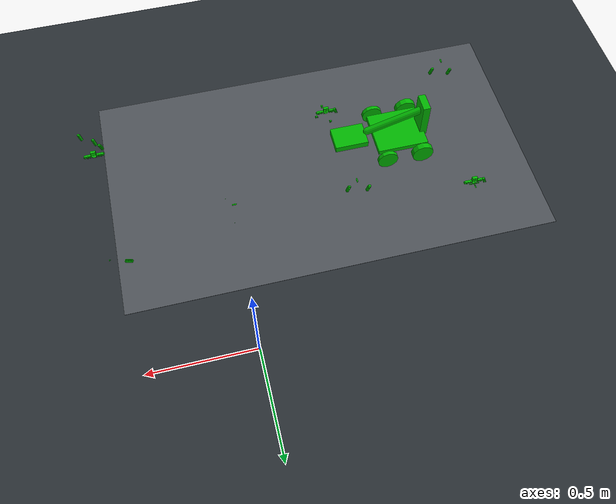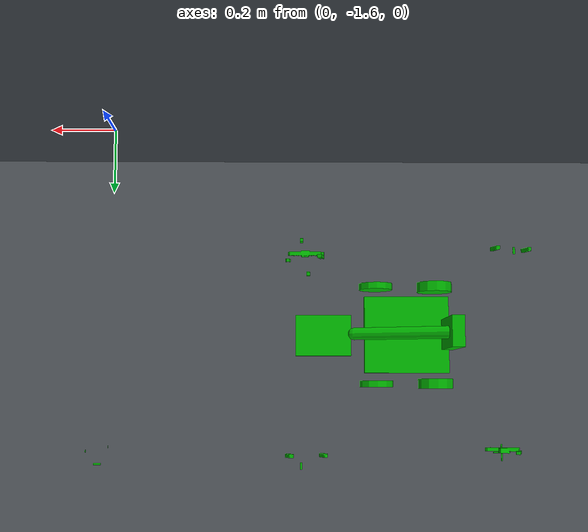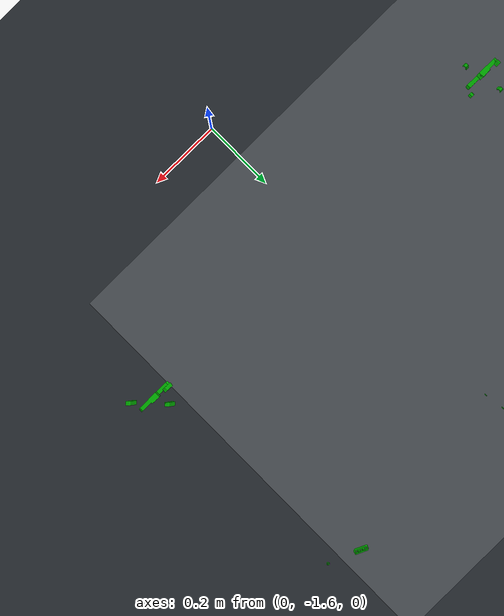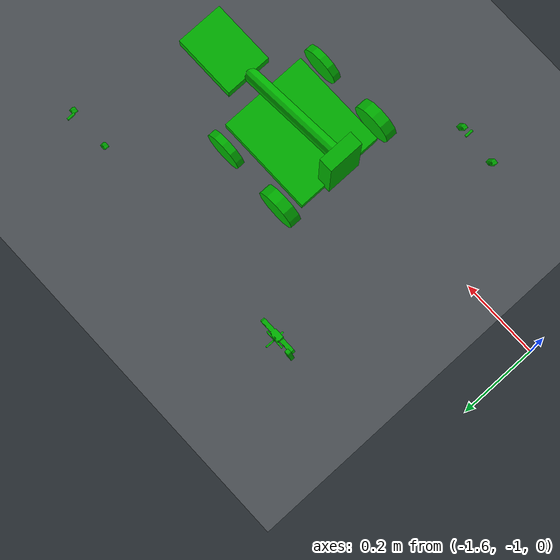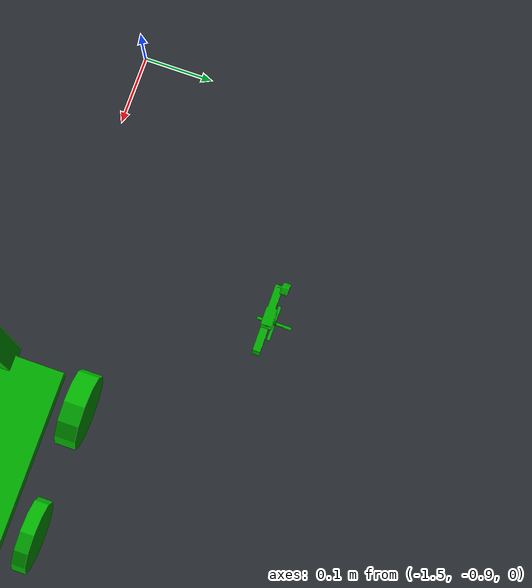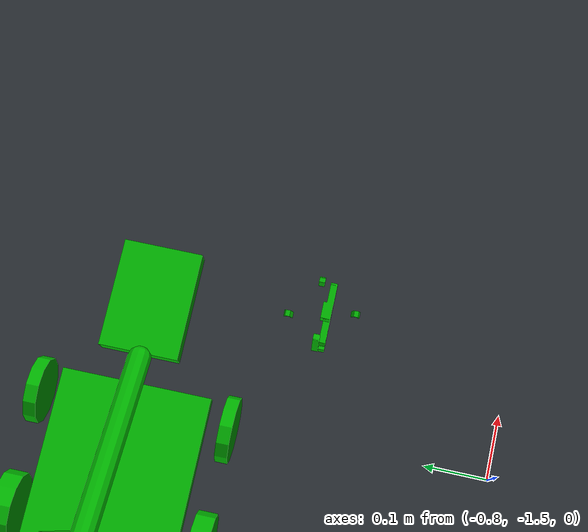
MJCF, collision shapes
<mujoco model="cad_field_and_clawbot"><compiler angle="radian" autolimits="true" /><option gravity="0 0 -9.81" timestep=".002" integrator="implicitfast" iterations="80" /><visual><global offwidth="1200" offheight="900" /><headlight ambient=".4 .4 .4" diffuse=".65 .65 .65" /></visual><asset><mesh name="field_p00034" file="/Users/joshuamichealscarano/Documents/AI-Vex-Project-1:5:26/data/cad_assets/override_field/parts/p00034.obj" scale=".001 .001 .001" inertia="shell" /><mesh name="field_p00035" file="/Users/joshuamichealscarano/Documents/AI-Vex-Project-1:5:26/data/cad_assets/override_field/parts/p00035.obj" scale=".001 .001 .001" inertia="shell" /><mesh name="field_p00036" file="/Users/joshuamichealscarano/Documents/AI-Vex-Project-1:5:26/data/cad_assets/override_field/parts/p00036.obj" scale=".001 .001 .001" inertia="shell" /><mesh name="field_p00037" file="/Users/joshuamichealscarano/Documents/AI-Vex-Project-1:5:26/data/cad_assets/override_field/parts/p00037.obj" scale=".001 .001 .001" inertia="shell" /><mesh name="field_p00038" file="/Users/joshuamichealscarano/Documents/AI-Vex-Project-1:5:26/data/cad_assets/override_field/parts/p00038.obj" scale=".001 .001 .001" inertia="shell" /><mesh name="field_p00041" file="/Users/joshuamichealscarano/Documents/AI-Vex-Project-1:5:26/data/cad_assets/override_field/parts/p00041.obj" scale=".001 .001 .001" inertia="shell" /><mesh name="field_p00043" file="/Users/joshuamichealscarano/Documents/AI-Vex-Project-1:5:26/data/cad_assets/override_field/parts/p00043.obj" scale=".001 .001 .001" inertia="shell" /><mesh name="field_p00044" file="/Users/joshuamichealscarano/Documents/AI-Vex-Project-1:5:26/data/cad_assets/override_field/parts/p00044.obj" scale=".001 .001 .001" inertia="shell" /><mesh name="field_p00045" file="/Users/joshuamichealscarano/Documents/AI-Vex-Project-1:5:26/data/cad_assets/override_field/parts/p00045.obj" scale=".001 .001 .001" inertia="shell" /><mesh name="field_p00047" file="/Users/joshuamichealscarano/Documents/AI-Vex-Project-1:5:26/data/cad_assets/override_field/parts/p00047.obj" scale=".001 .001 .001" inertia="shell" /><mesh name="field_p00059" file="/Users/joshuamichealscarano/Documents/AI-Vex-Project-1:5:26/data/cad_assets/override_field/parts/p00059.obj" scale=".001 .001 .001" inertia="shell" /><mesh name="field_p00060" file="/Users/joshuamichealscarano/Documents/AI-Vex-Project-1:5:26/data/cad_assets/override_field/parts/p00060.obj" scale=".001 .001 .001" inertia="shell" /><mesh name="field_p00062" file="/Users/joshuamichealscarano/Documents/AI-Vex-Project-1:5:26/data/cad_assets/override_field/parts/p00062.obj" scale=".001 .001 .001" inertia="shell" /><mesh name="field_p00063" file="/Users/joshuamichealscarano/Documents/AI-Vex-Project-1:5:26/data/cad_assets/override_field/parts/p00063.obj" scale=".001 .001 .001" inertia="shell" /><mesh name="field_p00065" file="/Users/joshuamichealscarano/Documents/AI-Vex-Project-1:5:26/data/cad_assets/override_field/parts/p00065.obj" scale=".001 .001 .001" inertia="shell" /><mesh name="robot_p00002" file="/Users/joshuamichealscarano/Documents/AI-Vex-Project-1:5:26/data/cad_assets/clawbot/parts/p00002.obj" scale=".001 .001 .001" inertia="shell" /><mesh name="robot_p00003" file="/Users/joshuamichealscarano/Documents/AI-Vex-Project-1:5:26/data/cad_assets/clawbot/parts/p00003.obj" scale=".001 .001 .001" inertia="shell" /><mesh name="robot_p00004" file="/Users/joshuamichealscarano/Documents/AI-Vex-Project-1:5:26/data/cad_assets/clawbot/parts/p00004.obj" scale=".001 .001 .001" inertia="shell" /><mesh name="robot_p00005" file="/Users/joshuamichealscarano/Documents/AI-Vex-Project-1:5:26/data/cad_assets/clawbot/parts/p00005.obj" scale=".001 .001 .001" inertia="shell" /><mesh name="robot_p00006" file="/Users/joshuamichealscarano/Documents/AI-Vex-Project-1:5:26/data/cad_assets/clawbot/parts/p00006.obj" scale=".001 .001 .001" inertia="shell" /><mesh name="robot_p00007" file="/Users/joshuamichealscarano/Documents/AI-Vex-Project-1:5:26/data/cad_assets/clawbot/parts/p00007.obj" scale=".001 .001 .001" inertia="shell" /><mesh name="robot_p00008" file="/Users/joshuamichealscarano/Documents/AI-Vex-Project-1:5:26/data/cad_assets/clawbot/parts/p00008.obj" scale=".001 .001 .001" inertia="shell" /><mesh name="robot_p00009" file="/Users/joshuamichealscarano/Documents/AI-Vex-Project-1:5:26/data/cad_assets/clawbot/parts/p00009.obj" scale=".001 .001 .001" inertia="shell" /><mesh name="robot_p00010" file="/Users/joshuamichealscarano/Documents/AI-Vex-Project-1:5:26/data/cad_assets/clawbot/parts/p00010.obj" scale=".001 .001 .001" inertia="shell" /><mesh name="robot_p00011" file="/Users/joshuamichealscarano/Documents/AI-Vex-Project-1:5:26/data/cad_assets/clawbot/parts/p00011.obj" scale=".001 .001 .001" inertia="shell" /><mesh name="robot_p00012" file="/Users/joshuamichealscarano/Documents/AI-Vex-Project-1:5:26/data/cad_assets/clawbot/parts/p00012.obj" scale=".001 .001 .001" inertia="shell" /><mesh name="robot_p00014" file="/Users/joshuamichealscarano/Documents/AI-Vex-Project-1:5:26/data/cad_assets/clawbot/parts/p00014.obj" scale=".001 .001 .001" inertia="shell" /><mesh name="robot_p00015" file="/Users/joshuamichealscarano/Documents/AI-Vex-Project-1:5:26/data/cad_assets/clawbot/parts/p00015.obj" scale=".001 .001 .001" inertia="shell" /><mesh name="robot_p00016" file="/Users/joshuamichealscarano/Documents/AI-Vex-Project-1:5:26/data/cad_assets/clawbot/parts/p00016.obj" scale=".001 .001 .001" inertia="shell" /><mesh name="robot_p00017" file="/Users/joshuamichealscarano/Documents/AI-Vex-Project-1:5:26/data/cad_assets/clawbot/parts/p00017.obj" scale=".001 .001 .001" inertia="shell" /><mesh name="robot_p00018" file="/Users/joshuamichealscarano/Documents/AI-Vex-Project-1:5:26/data/cad_assets/clawbot/parts/p00018.obj" scale=".001 .001 .001" inertia="shell" /><mesh name="robot_p00019" file="/Users/joshuamichealscarano/Documents/AI-Vex-Project-1:5:26/data/cad_assets/clawbot/parts/p00019.obj" scale=".001 .001 .001" inertia="shell" /><mesh name="robot_p00020" file="/Users/joshuamichealscarano/Documents/AI-Vex-Project-1:5:26/data/cad_assets/clawbot/parts/p00020.obj" scale=".001 .001 .001" inertia="shell" /><mesh name="robot_p00021" file="/Users/joshuamichealscarano/Documents/AI-Vex-Project-1:5:26/data/cad_assets/clawbot/parts/p00021.obj" scale=".001 .001 .001" inertia="shell" /><mesh name="robot_p00022" file="/Users/joshuamichealscarano/Documents/AI-Vex-Project-1:5:26/data/cad_assets/clawbot/parts/p00022.obj" scale=".001 .001 .001" inertia="shell" /><mesh name="robot_p00023" file="/Users/joshuamichealscarano/Documents/AI-Vex-Project-1:5:26/data/cad_assets/clawbot/parts/p00023.obj" scale=".001 .001 .001" inertia="shell" /><mesh name="robot_p00025" file="/Users/joshuamichealscarano/Documents/AI-Vex-Project-1:5:26/data/cad_assets/clawbot/parts/p00025.obj" scale=".001 .001 .001" inertia="shell" /><mesh name="robot_p00026" file="/Users/joshuamichealscarano/Documents/AI-Vex-Project-1:5:26/data/cad_assets/clawbot/parts/p00026.obj" scale=".001 .001 .001" inertia="shell" /><mesh name="robot_p00027" file="/Users/joshuamichealscarano/Documents/AI-Vex-Project-1:5:26/data/cad_assets/clawbot/parts/p00027.obj" scale=".001 .001 .001" inertia="shell" /><mesh name="robot_p00028" file="/Users/joshuamichealscarano/Documents/AI-Vex-Project-1:5:26/data/cad_assets/clawbot/parts/p00028.obj" scale=".001 .001 .001" inertia="shell" /><mesh name="robot_p00029" file="/Users/joshuamichealscarano/Documents/AI-Vex-Project-1:5:26/data/cad_assets/clawbot/parts/p00029.obj" scale=".001 .001 .001" inertia="shell" /><mesh name="robot_p00030" file="/Users/joshuamichealscarano/Documents/AI-Vex-Project-1:5:26/data/cad_assets/clawbot/parts/p00030.obj" scale=".001 .001 .001" inertia="shell" /><mesh name="robot_p00031" file="/Users/joshuamichealscarano/Documents/AI-Vex-Project-1:5:26/data/cad_assets/clawbot/parts/p00031.obj" scale=".001 .001 .001" inertia="shell" /><mesh name="robot_p00032" file="/Users/joshuamichealscarano/Documents/AI-Vex-Project-1:5:26/data/cad_assets/clawbot/parts/p00032.obj" scale=".001 .001 .001" inertia="shell" /><mesh name="robot_p00033" file="/Users/joshuamichealscarano/Documents/AI-Vex-Project-1:5:26/data/cad_assets/clawbot/parts/p00033.obj" scale=".001 .001 .001" inertia="shell" /><mesh name="robot_p00034" file="/Users/joshuamichealscarano/Documents/AI-Vex-Project-1:5:26/data/cad_assets/clawbot/parts/p00034.obj" scale=".001 .001 .001" inertia="shell" /><mesh name="robot_p00035" file="/Users/joshuamichealscarano/Documents/AI-Vex-Project-1:5:26/data/cad_assets/clawbot/parts/p00035.obj" scale=".001 .001 .001" inertia="shell" /><mesh name="robot_p00036" file="/Users/joshuamichealscarano/Documents/AI-Vex-Project-1:5:26/data/cad_assets/clawbot/parts/p00036.obj" scale=".001 .001 .001" inertia="shell" /><mesh name="robot_p00037" file="/Users/joshuamichealscarano/Documents/AI-Vex-Project-1:5:26/data/cad_assets/clawbot/parts/p00037.obj" scale=".001 .001 .001" inertia="shell" /><mesh name="robot_p00038" file="/Users/joshuamichealscarano/Documents/AI-Vex-Project-1:5:26/data/cad_assets/clawbot/parts/p00038.obj" scale=".001 .001 .001" inertia="shell" /><mesh name="robot_p00039" file="/Users/joshuamichealscarano/Documents/AI-Vex-Project-1:5:26/data/cad_assets/clawbot/parts/p00039.obj" scale=".001 .001 .001" inertia="shell" /><mesh name="robot_p00040" file="/Users/joshuamichealscarano/Documents/AI-Vex-Project-1:5:26/data/cad_assets/clawbot/parts/p00040.obj" scale=".001 .001 .001" inertia="shell" /><mesh name="robot_p00041" file="/Users/joshuamichealscarano/Documents/AI-Vex-Project-1:5:26/data/cad_assets/clawbot/parts/p00041.obj" scale=".001 .001 .001" inertia="shell" /><mesh name="robot_p00042" file="/Users/joshuamichealscarano/Documents/AI-Vex-Project-1:5:26/data/cad_assets/clawbot/parts/p00042.obj" scale=".001 .001 .001" inertia="shell" /><mesh name="robot_p00043" file="/Users/joshuamichealscarano/Documents/AI-Vex-Project-1:5:26/data/cad_assets/clawbot/parts/p00043.obj" scale=".001 .001 .001" inertia="shell" /><mesh name="robot_p00044" file="/Users/joshuamichealscarano/Documents/AI-Vex-Project-1:5:26/data/cad_assets/clawbot/parts/p00044.obj" scale=".001 .001 .001" inertia="shell" /><mesh name="robot_p00045" file="/Users/joshuamichealscarano/Documents/AI-Vex-Project-1:5:26/data/cad_assets/clawbot/parts/p00045.obj" scale=".001 .001 .001" inertia="shell" /><mesh name="robot_p00046" file="/Users/joshuamichealscarano/Documents/AI-Vex-Project-1:5:26/data/cad_assets/clawbot/parts/p00046.obj" scale=".001 .001 .001" inertia="shell" /><mesh name="robot_p00047" file="/Users/joshuamichealscarano/Documents/AI-Vex-Project-1:5:26/data/cad_assets/clawbot/parts/p00047.obj" scale=".001 .001 .001" inertia="shell" /><mesh name="robot_p00048" file="/Users/joshuamichealscarano/Documents/AI-Vex-Project-1:5:26/data/cad_assets/clawbot/parts/p00048.obj" scale=".001 .001 .001" inertia="shell" /><mesh name="robot_p00049" file="/Users/joshuamichealscarano/Documents/AI-Vex-Project-1:5:26/data/cad_assets/clawbot/parts/p00049.obj" scale=".001 .001 .001" inertia="shell" /><mesh name="robot_p00050" file="/Users/joshuamichealscarano/Documents/AI-Vex-Project-1:5:26/data/cad_assets/clawbot/parts/p00050.obj" scale=".001 .001 .001" inertia="shell" /><mesh name="robot_p00051" file="/Users/joshuamichealscarano/Documents/AI-Vex-Project-1:5:26/data/cad_assets/clawbot/parts/p00051.obj" scale=".001 .001 .001" inertia="shell" /><mesh name="robot_p00052" file="/Users/joshuamichealscarano/Documents/AI-Vex-Project-1:5:26/data/cad_assets/clawbot/parts/p00052.obj" scale=".001 .001 .001" inertia="shell" /><mesh name="robot_p00053" file="/Users/joshuamichealscarano/Documents/AI-Vex-Project-1:5:26/data/cad_assets/clawbot/parts/p00053.obj" scale=".001 .001 .001" inertia="shell" /><mesh name="robot_p00054" file="/Users/joshuamichealscarano/Documents/AI-Vex-Project-1:5:26/data/cad_assets/clawbot/parts/p00054.obj" scale=".001 .001 .001" inertia="shell" /><mesh name="robot_p00055" file="/Users/joshuamichealscarano/Documents/AI-Vex-Project-1:5:26/data/cad_assets/clawbot/parts/p00055.obj" scale=".001 .001 .001" inertia="shell" /><mesh name="robot_p00056" file="/Users/joshuamichealscarano/Documents/AI-Vex-Project-1:5:26/data/cad_assets/clawbot/parts/p00056.obj" scale=".001 .001 .001" inertia="shell" /><mesh name="robot_p00057" file="/Users/joshuamichealscarano/Documents/AI-Vex-Project-1:5:26/data/cad_assets/clawbot/parts/p00057.obj" scale=".001 .001 .001" inertia="shell" /><mesh name="robot_p00058" file="/Users/joshuamichealscarano/Documents/AI-Vex-Project-1:5:26/data/cad_assets/clawbot/parts/p00058.obj" scale=".001 .001 .001" inertia="shell" /><mesh name="robot_p00059" file="/Users/joshuamichealscarano/Documents/AI-Vex-Project-1:5:26/data/cad_assets/clawbot/parts/p00059.obj" scale=".001 .001 .001" inertia="shell" /><mesh name="robot_p00060" file="/Users/joshuamichealscarano/Documents/AI-Vex-Project-1:5:26/data/cad_assets/clawbot/parts/p00060.obj" scale=".001 .001 .001" inertia="shell" /><mesh name="robot_p00061" file="/Users/joshuamichealscarano/Documents/AI-Vex-Project-1:5:26/data/cad_assets/clawbot/parts/p00061.obj" scale=".001 .001 .001" inertia="shell" /><mesh name="robot_p00062" file="/Users/joshuamichealscarano/Documents/AI-Vex-Project-1:5:26/data/cad_assets/clawbot/parts/p00062.obj" scale=".001 .001 .001" inertia="shell" /><mesh name="robot_p00063" file="/Users/joshuamichealscarano/Documents/AI-Vex-Project-1:5:26/data/cad_assets/clawbot/parts/p00063.obj" scale=".001 .001 .001" inertia="shell" /><mesh name="robot_p00064" file="/Users/joshuamichealscarano/Documents/AI-Vex-Project-1:5:26/data/cad_assets/clawbot/parts/p00064.obj" scale=".001 .001 .001" inertia="shell" /><mesh name="robot_p00065" file="/Users/joshuamichealscarano/Documents/AI-Vex-Project-1:5:26/data/cad_assets/clawbot/parts/p00065.obj" scale=".001 .001 .001" inertia="shell" /><mesh name="robot_p00066" file="/Users/joshuamichealscarano/Documents/AI-Vex-Project-1:5:26/data/cad_assets/clawbot/parts/p00066.obj" scale=".001 .001 .001" inertia="shell" /><mesh name="robot_p00067" file="/Users/joshuamichealscarano/Documents/AI-Vex-Project-1:5:26/data/cad_assets/clawbot/parts/p00067.obj" scale=".001 .001 .001" inertia="shell" /><mesh name="robot_p00068" file="/Users/joshuamichealscarano/Documents/AI-Vex-Project-1:5:26/data/cad_assets/clawbot/parts/p00068.obj" scale=".001 .001 .001" inertia="shell" /></asset><worldbody><light pos="0 0 5" dir="0 0 -1" /><geom name="floor" type="plane" size="4 4 .1" group="3" rgba=".16 .18 .20 1" /><geom name="field_i00514" type="mesh" mesh="field_p00034" pos="0.5980585340001614 -1.1961170679999564 0.06399999999999945" quat="0.7071067811865476 0.7071067811865475 0.0 0.0" contype="0" conaffinity="0" mass="0" group="1" rgba=".46 .48 .52 1" /><geom name="contact_i00514" type="mesh" mesh="field_p00034" pos="0.5980585340001614 -1.1961170679999564 0.06399999999999945" quat="0.7071067811865476 0.7071067811865475 0.0 0.0" contype="1" conaffinity="2" group="3" rgba="0 .7 0 .15" mass="0" /><geom name="field_i00515" type="mesh" mesh="field_p00035" pos="0.5980585340001614 -1.1961170679999564 -0.01595000000000052" quat="0.7071067811865476 0.7071067811865475 0.0 0.0" contype="0" conaffinity="0" mass="0" group="1" rgba=".46 .48 .52 1" /><geom name="contact_i00515" type="mesh" mesh="field_p00035" pos="0.5980585340001614 -1.1961170679999564 -0.01595000000000052" quat="0.7071067811865476 0.7071067811865475 0.0 0.0" contype="1" conaffinity="2" group="3" rgba="0 .7 0 .15" mass="0" /><geom name="field_i00516" type="mesh" mesh="field_p00036" pos="0.5980585340001614 -1.1961170679999564 -4.996003610813204e-16" quat="0.7071067811865476 0.7071067811865475 0.0 0.0" contype="0" conaffinity="0" mass="0" group="1" rgba=".46 .48 .52 1" /><geom name="contact_i00516" type="mesh" mesh="field_p00036" pos="0.5980585340001614 -1.1961170679999564 -4.996003610813204e-16" quat="0.7071067811865476 0.7071067811865475 0.0 0.0" contype="1" conaffinity="2" group="3" rgba="0 .7 0 .15" mass="0" /><geom name="field_i00518" type="mesh" mesh="field_p00037" pos="0.5380585340001613 -1.1961170679999562 0.02589999999999948" quat="0.6123724356957951 0.6123724356957951 0.3535533905932728 0.35355339059327273" contype="0" conaffinity="0" mass="0" group="1" rgba=".46 .48 .52 1" /><geom name="contact_i00518" type="mesh" mesh="field_p00037" pos="0.5380585340001613 -1.1961170679999562 0.02589999999999948" quat="0.6123724356957951 0.6123724356957951 0.3535533905932728 0.35355339059327273" contype="1" conaffinity="2" group="3" rgba="0 .7 0 .15" mass="0" /><geom name="field_i00523" type="mesh" mesh="field_p00038" pos="0.5380585340001615 -1.1961170679999562 -0.01420000000000049" quat="0.0 0.9162477356257933 -0.40061214030606496 0.0" contype="0" conaffinity="0" mass="0" group="1" rgba=".46 .48 .52 1" /><geom name="field_i00526" type="mesh" mesh="field_p00038" pos="0.5380585340001615 -1.1961170679999562 0.06649999999999945" quat="0.9121810598040202 0.0 0.0 0.40978740114212214" contype="0" conaffinity="0" mass="0" group="1" rgba=".46 .48 .52 1" /><geom name="field_i00530" type="mesh" mesh="field_p00041" pos="0.5980585340001614 -1.1961170679999564 0.06399999999999945" quat="1.2519046104913231e-15 1.2157188858575955e-15 0.7071067811865476 0.7071067811865475" contype="0" conaffinity="0" mass="0" group="1" rgba=".46 .48 .52 1" /><geom name="contact_i00530" type="mesh" mesh="field_p00041" pos="0.5980585340001614 -1.1961170679999564 0.06399999999999945" quat="1.2519046104913231e-15 1.2157188858575955e-15 0.7071067811865476 0.7071067811865475" contype="1" conaffinity="2" group="3" rgba="0 .7 0 .15" mass="0" /><geom name="field_i00552" type="mesh" mesh="field_p00034" pos="-1.1961170679998343 -0.5980585339996403 -4.440892098500626e-16" quat="0.7071067811865476 0.7071067811865475 0.0 0.0" contype="0" conaffinity="0" mass="0" group="1" rgba=".46 .48 .52 1" /><geom name="contact_i00552" type="mesh" mesh="field_p00034" pos="-1.1961170679998343 -0.5980585339996403 -4.440892098500626e-16" quat="0.7071067811865476 0.7071067811865475 0.0 0.0" contype="1" conaffinity="2" group="3" rgba="0 .7 0 .15" mass="0" /><geom name="field_i00553" type="mesh" mesh="field_p00035" pos="-1.1961170679998343 -0.5980585339996403 -0.01645000000000052" quat="0.7071067811865476 0.7071067811865475 0.0 0.0" contype="0" conaffinity="0" mass="0" group="1" rgba=".46 .48 .52 1" /><geom name="contact_i00553" type="mesh" mesh="field_p00035" pos="-1.1961170679998343 -0.5980585339996403 -0.01645000000000052" quat="0.7071067811865476 0.7071067811865475 0.0 0.0" contype="1" conaffinity="2" group="3" rgba="0 .7 0 .15" mass="0" /><geom name="field_i00554" type="mesh" mesh="field_p00043" pos="-1.1961170679998343 -0.6580585339996404 -0.006350000000000466" quat="0.14803110976416547 0.14803110976416547 0.6914382044275464 0.6914382044275466" contype="0" conaffinity="0" mass="0" group="1" rgba=".46 .48 .52 1" /><geom name="field_i00555" type="mesh" mesh="field_p00044" pos="-1.1961170679998343 -0.6580585339996404 0.002499999999999558" quat="0.35524596286494614 0.0 0.0 0.9347728632497615" contype="0" conaffinity="0" mass="0" group="1" rgba=".46 .48 .52 1" /><geom name="field_i00556" type="mesh" mesh="field_p00044" pos="-1.1961170679998343 -0.6580585339996404 -0.014700000000000435" quat="0.0 0.28533392338519603 0.9584281674521107 0.0" contype="0" conaffinity="0" mass="0" group="1" rgba=".46 .48 .52 1" /><geom name="field_i00557" type="mesh" mesh="field_p00044" pos="-1.2561170679998344 -0.59805853399964 0.002499999999999558" quat="0.9121810598040202 0.0 0.0 0.40978740114212214" contype="0" conaffinity="0" mass="0" group="1" rgba=".46 .48 .52 1" /><geom name="field_i00558" type="mesh" mesh="field_p00044" pos="-1.1961170679998339 -0.5380585339996403 0.002499999999999558" quat="0.9347728632497603 0.0 0.0 -0.3552459628649494" contype="0" conaffinity="0" mass="0" group="1" rgba=".46 .48 .52 1" /><geom name="field_i00559" type="mesh" mesh="field_p00044" pos="-1.1361170679998343 -0.598058533999641 0.002499999999999558" quat="-0.409787401142119 0.0 0.0 0.9121810598040216" contype="0" conaffinity="0" mass="0" group="1" rgba=".46 .48 .52 1" /><geom name="field_i00560" type="mesh" mesh="field_p00044" pos="-1.2561170679998344 -0.59805853399964 -0.014700000000000435" quat="0.0 0.8794726086138192 0.475949504357347 0.0" contype="0" conaffinity="0" mass="0" group="1" rgba=".46 .48 .52 1" /><geom name="field_i00561" type="mesh" mesh="field_p00044" pos="-1.1961170679998339 -0.5380585339996402 -0.014700000000000435" quat="0.0 0.9584281674521098 -0.28533392338519936 0.0" contype="0" conaffinity="0" mass="0" group="1" rgba=".46 .48 .52 1" /><geom name="field_i00562" type="mesh" mesh="field_p00044" pos="-1.1361170679998343 -0.598058533999641 -0.014700000000000435" quat="0.0 -0.47594950435734396 0.8794726086138207 0.0" contype="0" conaffinity="0" mass="0" group="1" rgba=".46 .48 .52 1" /><geom name="field_i00563" type="mesh" mesh="field_p00043" pos="-1.2561170679998344 -0.59805853399964 -0.006350000000000466" quat="0.5935944446629806 0.5935944446629807 0.3842468415813559 0.3842468415813559" contype="0" conaffinity="0" mass="0" group="1" rgba=".46 .48 .52 1" /><geom name="field_i00564" type="mesh" mesh="field_p00043" pos="-1.1961170679998339 -0.5380585339996403 -0.006350000000000466" quat="0.691438204427546 0.691438204427546 -0.1480311097641679 -0.1480311097641679" contype="0" conaffinity="0" mass="0" group="1" rgba=".46 .48 .52 1" /><geom name="field_i00565" type="mesh" mesh="field_p00043" pos="-1.1361170679998343 -0.598058533999641 -0.006350000000000466" quat="-0.38424684158135375 -0.38424684158135375 0.593594444662982 0.5935944446629821" contype="0" conaffinity="0" mass="0" group="1" rgba=".46 .48 .52 1" /><geom name="field_i00566" type="mesh" mesh="field_p00045" pos="-1.1961170679998343 -0.5980585339996403 -4.440892098500626e-16" quat="0.5 0.5 -0.5 -0.5" contype="0" conaffinity="0" mass="0" group="1" rgba=".46 .48 .52 1" /><geom name="contact_i00566" type="mesh" mesh="field_p00045" pos="-1.1961170679998343 -0.5980585339996403 -4.440892098500626e-16" quat="0.5 0.5 -0.5 -0.5" contype="1" conaffinity="2" group="3" rgba="0 .7 0 .15" mass="0" /><geom name="field_i00567" type="mesh" mesh="field_p00045" pos="-1.1961170679998343 -0.5980585339996403 -4.440892098500626e-16" quat="1.2519046104913231e-15 1.2157188858575955e-15 0.7071067811865476 0.7071067811865475" contype="0" conaffinity="0" mass="0" group="1" rgba=".46 .48 .52 1" /><geom name="contact_i00567" type="mesh" mesh="field_p00045" pos="-1.1961170679998343 -0.5980585339996403 -4.440892098500626e-16" quat="1.2519046104913231e-15 1.2157188858575955e-15 0.7071067811865476 0.7071067811865475" contype="1" conaffinity="2" group="3" rgba="0 .7 0 .15" mass="0" /><geom name="field_i00568" type="mesh" mesh="field_p00045" pos="-1.1961170679998343 -0.5980585339996403 -4.440892098500626e-16" quat="0.5000000000000017 0.5000000000000018 0.49999999999999833 0.49999999999999833" contype="0" conaffinity="0" mass="0" group="1" rgba=".46 .48 .52 1" /><geom name="contact_i00568" type="mesh" mesh="field_p00045" pos="-1.1961170679998343 -0.5980585339996403 -4.440892098500626e-16" quat="0.5000000000000017 0.5000000000000018 0.49999999999999833 0.49999999999999833" contype="1" conaffinity="2" group="3" rgba="0 .7 0 .15" mass="0" /><geom name="field_i00569" type="mesh" mesh="field_p00045" pos="-1.1961170679998343 -0.5980585339996403 -4.440892098500626e-16" quat="0.7071067811865476 0.7071067811865475 0.0 0.0" contype="0" conaffinity="0" mass="0" group="1" rgba=".46 .48 .52 1" /><geom name="contact_i00569" type="mesh" mesh="field_p00045" pos="-1.1961170679998343 -0.5980585339996403 -4.440892098500626e-16" quat="0.7071067811865476 0.7071067811865475 0.0 0.0" contype="1" conaffinity="2" group="3" rgba="0 .7 0 .15" mass="0" /><geom name="field_i00570" type="mesh" mesh="field_p00034" pos="-0.5980585339998384 -1.1961170679997752 -3.885780586188048e-16" quat="0.7071067811865476 0.7071067811865475 0.0 0.0" contype="0" conaffinity="0" mass="0" group="1" rgba=".46 .48 .52 1" /><geom name="contact_i00570" type="mesh" mesh="field_p00034" pos="-0.5980585339998384 -1.1961170679997752 -3.885780586188048e-16" quat="0.7071067811865476 0.7071067811865475 0.0 0.0" contype="1" conaffinity="2" group="3" rgba="0 .7 0 .15" mass="0" /><geom name="field_i00571" type="mesh" mesh="field_p00035" pos="-0.5980585339998384 -1.1961170679997752 -0.016450000000000464" quat="0.7071067811865476 0.7071067811865475 0.0 0.0" contype="0" conaffinity="0" mass="0" group="1" rgba=".46 .48 .52 1" /><geom name="contact_i00571" type="mesh" mesh="field_p00035" pos="-0.5980585339998384 -1.1961170679997752 -0.016450000000000464" quat="0.7071067811865476 0.7071067811865475 0.0 0.0" contype="1" conaffinity="2" group="3" rgba="0 .7 0 .15" mass="0" /><geom name="field_i00572" type="mesh" mesh="field_p00043" pos="-0.5980585339998384 -1.256117067999775 -0.006350000000000355" quat="0.14803110976416547 0.14803110976416547 0.6914382044275464 0.6914382044275466" contype="0" conaffinity="0" mass="0" group="1" rgba=".46 .48 .52 1" /><geom name="field_i00573" type="mesh" mesh="field_p00044" pos="-0.5980585339998384 -1.256117067999775 0.0024999999999996136" quat="0.35524596286494614 0.0 0.0 0.9347728632497615" contype="0" conaffinity="0" mass="0" group="1" rgba=".46 .48 .52 1" /><geom name="field_i00574" type="mesh" mesh="field_p00044" pos="-0.5980585339998384 -1.256117067999775 -0.014700000000000435" quat="0.0 0.28533392338519603 0.9584281674521107 0.0" contype="0" conaffinity="0" mass="0" group="1" rgba=".46 .48 .52 1" /><geom name="field_i00575" type="mesh" mesh="field_p00044" pos="-0.6580585339998385 -1.196117067999775 0.0024999999999996136" quat="0.9121810598040202 0.0 0.0 0.40978740114212214" contype="0" conaffinity="0" mass="0" group="1" rgba=".46 .48 .52 1" /><geom name="field_i00576" type="mesh" mesh="field_p00044" pos="-0.598058533999838 -1.1361170679997752 0.0024999999999996136" quat="0.9347728632497603 0.0 0.0 -0.3552459628649494" contype="0" conaffinity="0" mass="0" group="1" rgba=".46 .48 .52 1" /><geom name="field_i00577" type="mesh" mesh="field_p00044" pos="-0.5380585339998385 -1.196117067999776 0.0024999999999996136" quat="-0.409787401142119 0.0 0.0 0.9121810598040216" contype="0" conaffinity="0" mass="0" group="1" rgba=".46 .48 .52 1" /><geom name="field_i00578" type="mesh" mesh="field_p00044" pos="-0.6580585339998385 -1.196117067999775 -0.014700000000000435" quat="0.0 0.8794726086138192 0.475949504357347 0.0" contype="0" conaffinity="0" mass="0" group="1" rgba=".46 .48 .52 1" /><geom name="field_i00579" type="mesh" mesh="field_p00044" pos="-0.598058533999838 -1.1361170679997752 -0.014700000000000435" quat="0.0 0.9584281674521098 -0.28533392338519936 0.0" contype="0" conaffinity="0" mass="0" group="1" rgba=".46 .48 .52 1" /><geom name="field_i00580" type="mesh" mesh="field_p00044" pos="-0.5380585339998385 -1.196117067999776 -0.014700000000000435" quat="0.0 -0.47594950435734396 0.8794726086138207 0.0" contype="0" conaffinity="0" mass="0" group="1" rgba=".46 .48 .52 1" /><geom name="field_i00581" type="mesh" mesh="field_p00043" pos="-0.6580585339998384 -1.196117067999775 -0.006350000000000355" quat="0.5935944446629806 0.5935944446629807 0.3842468415813559 0.3842468415813559" contype="0" conaffinity="0" mass="0" group="1" rgba=".46 .48 .52 1" /><geom name="field_i00582" type="mesh" mesh="field_p00043" pos="-0.598058533999838 -1.1361170679997752 -0.006350000000000355" quat="0.691438204427546 0.691438204427546 -0.1480311097641679 -0.1480311097641679" contype="0" conaffinity="0" mass="0" group="1" rgba=".46 .48 .52 1" /><geom name="field_i00583" type="mesh" mesh="field_p00043" pos="-0.5380585339998386 -1.196117067999776 -0.006350000000000355" quat="-0.38424684158135375 -0.38424684158135375 0.593594444662982 0.5935944446629821" contype="0" conaffinity="0" mass="0" group="1" rgba=".46 .48 .52 1" /><geom name="field_i00584" type="mesh" mesh="field_p00047" pos="-0.5980585339998384 -1.1961170679997752 -3.885780586188048e-16" quat="0.5 0.5 -0.5 -0.5" contype="0" conaffinity="0" mass="0" group="1" rgba=".46 .48 .52 1" /><geom name="contact_i00584" type="mesh" mesh="field_p00047" pos="-0.5980585339998384 -1.1961170679997752 -3.885780586188048e-16" quat="0.5 0.5 -0.5 -0.5" contype="1" conaffinity="2" group="3" rgba="0 .7 0 .15" mass="0" /><geom name="field_i00585" type="mesh" mesh="field_p00047" pos="-0.5980585339998384 -1.1961170679997752 -3.885780586188048e-16" quat="1.2519046104913231e-15 1.2157188858575955e-15 0.7071067811865476 0.7071067811865475" contype="0" conaffinity="0" mass="0" group="1" rgba=".46 .48 .52 1" /><geom name="contact_i00585" type="mesh" mesh="field_p00047" pos="-0.5980585339998384 -1.1961170679997752 -3.885780586188048e-16" quat="1.2519046104913231e-15 1.2157188858575955e-15 0.7071067811865476 0.7071067811865475" contype="1" conaffinity="2" group="3" rgba="0 .7 0 .15" mass="0" /><geom name="field_i00586" type="mesh" mesh="field_p00047" pos="-0.5980585339998384 -1.1961170679997752 -3.885780586188048e-16" quat="0.5000000000000017 0.5000000000000018 0.49999999999999833 0.49999999999999833" contype="0" conaffinity="0" mass="0" group="1" rgba=".46 .48 .52 1" /><geom name="contact_i00586" type="mesh" mesh="field_p00047" pos="-0.5980585339998384 -1.1961170679997752 -3.885780586188048e-16" quat="0.5000000000000017 0.5000000000000018 0.49999999999999833 0.49999999999999833" contype="1" conaffinity="2" group="3" rgba="0 .7 0 .15" mass="0" /><geom name="field_i00587" type="mesh" mesh="field_p00047" pos="-0.5980585339998384 -1.1961170679997752 -3.885780586188048e-16" quat="0.7071067811865476 0.7071067811865475 0.0 0.0" contype="0" conaffinity="0" mass="0" group="1" rgba=".46 .48 .52 1" /><geom name="contact_i00587" type="mesh" mesh="field_p00047" pos="-0.5980585339998384 -1.1961170679997752 -3.885780586188048e-16" quat="0.7071067811865476 0.7071067811865475 0.0 0.0" contype="1" conaffinity="2" group="3" rgba="0 .7 0 .15" mass="0" /><geom name="field_i00651" type="mesh" mesh="field_p00062" pos="2.6364347827690625e-13 -0.5980585339996574 0.16728264999999595" quat="-0.49999999999996203 0.49999999999996203 -0.500000000000038 0.500000000000038" contype="0" conaffinity="0" mass="0" group="1" rgba=".65 .8 .88 .45" /><geom name="contact_i00651" type="mesh" mesh="field_p00062" pos="2.6364347827690625e-13 -0.5980585339996574 0.16728264999999595" quat="-0.49999999999996203 0.49999999999996203 -0.500000000000038 0.500000000000038" contype="1" conaffinity="2" group="3" rgba="0 .7 0 .15" mass="0" /><geom name="field_i00652" type="mesh" mesh="field_p00063" pos="2.6365763347002605e-13 -0.5980585339996574 -0.0027173500000040596" quat="0.5000000000000758 0.5000000000000759 0.49999999999992417 0.49999999999992417" contype="0" conaffinity="0" mass="0" group="1" rgba=".46 .48 .52 1" /><geom name="contact_i00652" type="mesh" mesh="field_p00063" pos="2.6365763347002605e-13 -0.5980585339996574 -0.0027173500000040596" quat="0.5000000000000758 0.5000000000000759 0.49999999999992417 0.49999999999992417" contype="1" conaffinity="2" group="3" rgba="0 .7 0 .15" mass="0" /><geom name="field_i00653" type="mesh" mesh="field_p00059" pos="2.636019645341641e-13 -0.5980585339996574 0.16728264999999587" quat="-0.49999999999996203 0.49999999999996203 -0.500000000000038 0.500000000000038" contype="0" conaffinity="0" mass="0" group="1" rgba=".025 .3 .72 1" /><geom name="contact_i00653" type="mesh" mesh="field_p00059" pos="2.636019645341641e-13 -0.5980585339996574 0.16728264999999587" quat="-0.49999999999996203 0.49999999999996203 -0.500000000000038 0.500000000000038" contype="1" conaffinity="2" group="3" rgba="0 .7 0 .15" mass="0" /><geom name="field_i00654" type="mesh" mesh="field_p00060" pos="2.636019645341641e-13 -0.5980585339996574 0.16728264999999587" quat="0.500000000000038 0.500000000000038 0.49999999999996203 0.49999999999996203" contype="0" conaffinity="0" mass="0" group="1" rgba=".65 .035 .055 1" /><geom name="contact_i00654" type="mesh" mesh="field_p00060" pos="2.636019645341641e-13 -0.5980585339996574 0.16728264999999587" quat="0.500000000000038 0.500000000000038 0.49999999999996203 0.49999999999996203" contype="1" conaffinity="2" group="3" rgba="0 .7 0 .15" mass="0" /><geom name="field_i00667" type="mesh" mesh="field_p00065" pos="-1.1961170680002877 -1.1961170679993218 0.16728265000004078" quat="0.7071067811865476 0.7071067811865475 -2.3692235117105774e-16 -7.958613471523303e-17" contype="0" conaffinity="0" mass="0" group="1" rgba=".9 .68 .035 1" /><geom name="contact_i00667" type="mesh" mesh="field_p00065" pos="-1.1961170680002877 -1.1961170679993218 0.16728265000004078" quat="0.7071067811865476 0.7071067811865475 -2.3692235117105774e-16 -7.958613471523303e-17" contype="1" conaffinity="2" group="3" rgba="0 .7 0 .15" mass="0" /><geom name="field_i00668" type="mesh" mesh="field_p00065" pos="-1.1961170680002877 -1.1961170679993218 0.16728265000004078" quat="-7.958613471523303e-17 2.3692235117105774e-16 0.7071067811865476 -0.7071067811865475" contype="0" conaffinity="0" mass="0" group="1" rgba=".9 .68 .035 1" /><geom name="contact_i00668" type="mesh" mesh="field_p00065" pos="-1.1961170680002877 -1.1961170679993218 0.16728265000004078" quat="-7.958613471523303e-17 2.3692235117105774e-16 0.7071067811865476 -0.7071067811865475" contype="1" conaffinity="2" group="3" rgba="0 .7 0 .15" mass="0" /><geom name="field_i00934" type="mesh" mesh="field_p00060" pos="0.48032896590521745 -0.5980585339995844 0.0356316174765125" quat="-0.09212966890525441 -0.701079256651777 0.7010792566517771 0.09212966890525467" contype="0" conaffinity="0" mass="0" group="1" rgba=".65 .035 .055 1" /><geom name="contact_i00934" type="mesh" mesh="field_p00060" pos="0.48032896590521745 -0.5980585339995844 0.0356316174765125" quat="-0.09212966890525441 -0.701079256651777 0.7010792566517771 0.09212966890525467" contype="1" conaffinity="2" group="3" rgba="0 .7 0 .15" mass="0" /><geom name="field_i00935" type="mesh" mesh="field_p00065" pos="0.48032896590521745 -0.5980585339995844 0.0356316174765125" quat="-0.09212966890525467 0.7010792566517771 0.701079256651777 -0.09212966890525441" contype="0" conaffinity="0" mass="0" group="1" rgba=".9 .68 .035 1" /><geom name="contact_i00935" type="mesh" mesh="field_p00065" pos="0.48032896590521745 -0.5980585339995844 0.0356316174765125" quat="-0.09212966890525467 0.7010792566517771 0.701079256651777 -0.09212966890525441" contype="1" conaffinity="2" group="3" rgba="0 .7 0 .15" mass="0" /><geom name="field_i00976" type="mesh" mesh="field_p00062" pos="-1.196117067999925 -1.1961170679996846 0.16728265000004072" quat="8.663840939877317e-22 9.803720294090994e-22 -0.7071067811865475 0.7071067811865476" contype="0" conaffinity="0" mass="0" group="1" rgba=".65 .8 .88 .45" /><geom name="contact_i00976" type="mesh" mesh="field_p00062" pos="-1.196117067999925 -1.1961170679996846 0.16728265000004072" quat="8.663840939877317e-22 9.803720294090994e-22 -0.7071067811865475 0.7071067811865476" contype="1" conaffinity="2" group="3" rgba="0 .7 0 .15" mass="0" /><geom name="field_i00977" type="mesh" mesh="field_p00063" pos="-1.196117067999925 -1.1961170679996846 -0.0027173499999593176" quat="0.7071067811865476 0.7071067811865475 -5.3604875895987894e-14 -5.3604876819365714e-14" contype="0" conaffinity="0" mass="0" group="1" rgba=".46 .48 .52 1" /><geom name="contact_i00977" type="mesh" mesh="field_p00063" pos="-1.196117067999925 -1.1961170679996846 -0.0027173499999593176" quat="0.7071067811865476 0.7071067811865475 -5.3604875895987894e-14 -5.3604876819365714e-14" contype="1" conaffinity="2" group="3" rgba="0 .7 0 .15" mass="0" /><geom name="field_i00978" type="mesh" mesh="field_p00062" pos="-0.5980585339997478 -0.5980585339997311 0.16728265000002066" quat="-5.699443763099093e-23 5.699349779037684e-23 -0.7071067811865475 0.7071067811865476" contype="0" conaffinity="0" mass="0" group="1" rgba=".65 .8 .88 .45" /><geom name="contact_i00978" type="mesh" mesh="field_p00062" pos="-0.5980585339997478 -0.5980585339997311 0.16728265000002066" quat="-5.699443763099093e-23 5.699349779037684e-23 -0.7071067811865475 0.7071067811865476" contype="1" conaffinity="2" group="3" rgba="0 .7 0 .15" mass="0" /><geom name="field_i00979" type="mesh" mesh="field_p00063" pos="-0.5980585339997478 -0.5980585339997311 -0.002717349999979357" quat="0.7071067811865476 0.7071067811865475 -5.360487681936643e-14 -5.360487589598718e-14" contype="0" conaffinity="0" mass="0" group="1" rgba=".46 .48 .52 1" /><geom name="contact_i00979" type="mesh" mesh="field_p00063" pos="-0.5980585339997478 -0.5980585339997311 -0.002717349999979357" quat="0.7071067811865476 0.7071067811865475 -5.360487681936643e-14 -5.360487589598718e-14" contype="1" conaffinity="2" group="3" rgba="0 .7 0 .15" mass="0" /><geom name="field_i01016" type="mesh" mesh="field_p00065" pos="-0.5980585339999291 -0.5980585339995497 0.16728265000002054" quat="0.7071067811865476 0.7071067811865475 0.0 0.0" contype="0" conaffinity="0" mass="0" group="1" rgba=".9 .68 .035 1" /><geom name="contact_i01016" type="mesh" mesh="field_p00065" pos="-0.5980585339999291 -0.5980585339995497 0.16728265000002054" quat="0.7071067811865476 0.7071067811865475 0.0 0.0" contype="1" conaffinity="2" group="3" rgba="0 .7 0 .15" mass="0" /><geom name="field_i01017" type="mesh" mesh="field_p00065" pos="-0.5980585339999291 -0.5980585339995497 0.16728265000002054" quat="0.0 0.0 -0.7071067811865475 0.7071067811865476" contype="0" conaffinity="0" mass="0" group="1" rgba=".9 .68 .035 1" /><geom name="contact_i01017" type="mesh" mesh="field_p00065" pos="-0.5980585339999291 -0.5980585339995497 0.16728265000002054" quat="0.0 0.0 -0.7071067811865475 0.7071067811865476" contype="1" conaffinity="2" group="3" rgba="0 .7 0 .15" mass="0" /><geom name="field_i01018" type="mesh" mesh="field_p00065" pos="0.5980585340005239 -1.1961170679997755 0.14849999999999947" quat="0.2705980500730985 0.27059805007309856 0.6532814824381883 0.6532814824381882" contype="0" conaffinity="0" mass="0" group="1" rgba=".9 .68 .035 1" /><geom name="contact_i01018" type="mesh" mesh="field_p00065" pos="0.5980585340005239 -1.1961170679997755 0.14849999999999947" quat="0.2705980500730985 0.27059805007309856 0.6532814824381883 0.6532814824381882" contype="1" conaffinity="2" group="3" rgba="0 .7 0 .15" mass="0" /><geom name="field_i01019" type="mesh" mesh="field_p00065" pos="0.5980585340005239 -1.1961170679997755 0.14849999999999947" quat="0.6532814824381882 -0.6532814824381883 0.27059805007309856 -0.27059805007309845" contype="0" conaffinity="0" mass="0" group="1" rgba=".9 .68 .035 1" /><geom name="contact_i01019" type="mesh" mesh="field_p00065" pos="0.5980585340005239 -1.1961170679997755 0.14849999999999947" quat="0.6532814824381882 -0.6532814824381883 0.27059805007309856 -0.27059805007309845" contype="1" conaffinity="2" group="3" rgba="0 .7 0 .15" mass="0" /><body name="robot" pos="-.9 -.95 .056"><freejoint name="root" /><geom name="frame_contact" type="box" pos="0 0 .018" size=".126 .114 .012" mass="1.35" group="3" contype="2" conaffinity="1" rgba="0 .7 0 .2" /><geom name="battery_mass" type="box" pos="-.1 -.014 .01" size=".024 .08 .015" mass="0.35" group="3" contype="0" conaffinity="0" rgba="0 0 0 0" /><geom name="fixed_arm_mass" type="box" pos=".06 0 .115" size=".13 .025 .018" mass="0.65" group="3" contype="0" conaffinity="0" rgba="0 0 0 0" /><geom name="fixed_claw_contact" type="box" pos=".25 .005 .042" size=".082 .06 .016" mass="0" group="3" contype="2" conaffinity="1" rgba="0 .7 0 .2" /><geom name="arm_contact" type="capsule" fromto="-.122 0 .149 .16 0 .06" size=".018" mass="0" group="3" contype="2" conaffinity="1" rgba="0 .7 0 .2" /><geom name="mast_contact" type="box" pos="-.122 0 .105" size=".018 .045 .095" mass="0" group="3" contype="2" conaffinity="1" rgba="0 .7 0 .2" /><geom name="robot_i00000" type="mesh" mesh="robot_p00002" pos="0.09847540173296032 0.0604769392803896 -2.5714674735626344e-05" quat="3.334775382891007e-17 1.7181433922416647e-15 2.6074219964273e-15 1.0" contype="0" conaffinity="0" mass="0" group="1" rgba="0.01850022003054619 0.021219009533524513 0.023153366521000862 1" /><geom name="robot_i00001" type="mesh" mesh="robot_p00003" pos="0.10162536980693931 0.1274519392803905 -2.567789359315606e-05" quat="0.5000000000000012 -0.4999999999999988 -0.49999999999999956 0.5000000000000004" contype="0" conaffinity="0" mass="0" group="1" rgba="0.13286831974983215 0.13286831974983215 0.13286831974983215 1" /><geom name="robot_i00002" type="mesh" mesh="robot_p00004" pos="0.08892536492067532 0.13698943928039048 -2.5686186142567097e-05" quat="0.7013456129747524 0.7013456129747518 -0.09007958237619262 0.09007958237619197" contype="0" conaffinity="0" mass="0" group="1" rgba="0.8227857351303101 0.8227857351303101 0.8227857351303101 1" /><geom name="robot_i00003" type="mesh" mesh="robot_p00005" pos="-0.06870690124986709 0.1207019392803905 0.014782196268336633" quat="-7.997658461420492e-16 -0.7071067811865475 7.997658461420492e-16 0.7071067811865476" contype="0" conaffinity="0" mass="0" group="1" rgba="0.7912979125976562 0.7912979125976562 0.7912979125976562 1" /><geom name="robot_i00004" type="mesh" mesh="robot_p00004" pos="-0.08892530124986711 0.1306394392803905 2.4996268336583208e-05" quat="-0.28744373618483376 0.28744373618483204 0.6460465142140333 0.646046514214035" contype="0" conaffinity="0" mass="0" group="1" rgba="0.8227857351303101 0.8227857351303101 0.8227857351303101 1" /><geom name="robot_i00005" type="mesh" mesh="robot_p00006" pos="-0.10801850626531498 0.10192317611757651 -1.917817721864591e-05" quat="0.6977307193850331 0.7162406181305105 -0.009372891440620847 -0.009130666597286166" contype="0" conaffinity="0" mass="0" group="1" rgba="0.07421357184648514 0.07421357184648514 0.07421357184648514 1" /><geom name="robot_i00006" type="mesh" mesh="robot_p00004" pos="-0.08892530124986721 -0.13053556071960948 2.4996268337143523e-05" quat="-0.18023609565446094 -0.18023609565445992 -0.6837506488649452 0.6837506488649491" contype="0" conaffinity="0" mass="0" group="1" rgba="0.8227857351303101 0.8227857351303101 0.8227857351303101 1" /><geom name="robot_i00007" type="mesh" mesh="robot_p00007" pos="-0.12087530124986669 5.193928039066986e-05 0.022274996268337184" quat="-5.132757762306371e-16 0.7071067811865476 0.7071067811865475 -1.916545911179263e-15" contype="0" conaffinity="0" mass="0" group="1" rgba="0.7912979125976562 0.7912979125976562 0.7912979125976562 1" /><geom name="robot_i00008" type="mesh" mesh="robot_p00008" pos="-0.101325301249867 -0.0824980607196095 0.011674996268337264" quat="-1.718143392241685e-15 1.5956287909886566e-30 1.0 -1.269817584415025e-15" contype="0" conaffinity="0" mass="0" group="1" rgba="0.07421357184648514 0.07421357184648514 0.07421357184648514 1" /><geom name="robot_i00009" type="mesh" mesh="robot_p00009" pos="-0.10117474815398259 -0.014518073773545697 0.0039249962683369725" quat="2.069509665702966e-15 0.7071067811865476 -0.7071067811865475 -2.7371641608338823e-16" contype="0" conaffinity="0" mass="0" group="1" rgba="0.01850022003054619 0.021219009533524513 0.023153366521000862 1" /><body name="wheel_i00010" pos="0.0889251949408463 -0.14673528002961397 -2.5748426602396002e-05"><joint name="wheel_i00010" type="hinge" axis="0 1 0" damping=".001" armature=".00002" /><geom name="robot_i00010" type="mesh" mesh="robot_p00010" pos="0.0 9.419915425348813e-05 0.0" quat="-2.0293389754430299e-16 -0.08802630327534827 2.9172759690976574e-15 0.996118150588411" contype="0" conaffinity="0" mass="0" group="1" rgba="0.13286831974983215 0.13286831974983215 0.13286831974983215 1" /><geom name="wheel_i00010_contact" type="cylinder" size="0.0508 0.009619226466510096" quat=".7071067812 .7071067812 0 0" mass="0.12" friction=".8 .001 .00005" priority="1" group="3" contype="2" conaffinity="1" rgba="0 .7 0 .2" /></body><geom name="robot_i00011" type="mesh" mesh="robot_p00003" pos="0.10162536980694731 -0.10154806071960949 -2.567493359417576e-05" quat="0.4999999999999989 0.5000000000000011 0.5000000000000006 0.49999999999999956" contype="0" conaffinity="0" mass="0" group="1" rgba="0.13286831974983215 0.13286831974983215 0.13286831974983215 1" /><geom name="robot_i00012" type="mesh" mesh="robot_p00011" pos="-0.018795901249866687 -0.006298060719609187 0.012958277778336934" quat="0.7071067811865476 -7.212612232078573e-16 -7.212612232078573e-16 -0.7071067811865475" contype="0" conaffinity="0" mass="0" group="1" rgba="0.01850022003054619 0.021219009533524513 0.023153366521000862 1" /><body name="wheel_i00013" pos="-0.08892524967493061 -0.14547136868638744 2.5725903315333275e-05"><joint name="wheel_i00013" type="hinge" axis="0 1 0" damping=".001" armature=".00002" /><geom name="robot_i00013" type="mesh" mesh="robot_p00012" pos="2.6020852139652106e-18 0.006998307966777917 -3.9898639947466563e-17" quat="0.5035145532104867 -1.468045305130825e-15 -0.8639867445194076 2.466127429910771e-15" contype="0" conaffinity="0" mass="0" group="1" rgba="0.07421357184648514 0.07421357184648514 0.07421357184648514 1" /><geom name="wheel_i00013_contact" type="cylinder" size="0.05305 0.014546827525108554" quat=".7071067812 .7071067812 0 0" mass="0.12" friction=".04 .001 .00005" priority="1" group="3" contype="2" conaffinity="1" rgba="0 .7 0 .2" /></body><geom name="robot_i00014" type="mesh" mesh="robot_p00004" pos="0.0889253665457943 -0.13053556071960948 -2.566501592193675e-05" quat="0.5420722269318813 0.542072226931878 0.45404592365653007 -0.45404592365653285" contype="0" conaffinity="0" mass="0" group="1" rgba="0.8227857351303101 0.8227857351303101 0.8227857351303101 1" /><geom name="robot_i00015" type="mesh" mesh="robot_p00008" pos="-0.101325301249867 0.04450193928039051 0.011674996268337004" quat="-1.718143392241685e-15 1.5956287909886566e-30 1.0 -1.269817584415025e-15" contype="0" conaffinity="0" mass="0" group="1" rgba="0.07421357184648514 0.07421357184648514 0.07421357184648514 1" /><geom name="robot_i00016" type="mesh" mesh="robot_p00006" pos="-0.10797530124986718 -0.12744361319812347 2.4996268337212912e-05" quat="0.7071067811865496 0.7071067811865455 1.3130416223726868e-15 -1.1167800650372129e-15" contype="0" conaffinity="0" mass="0" group="1" rgba="0.07421357184648514 0.07421357184648514 0.07421357184648514 1" /><geom name="robot_i00017" type="mesh" mesh="robot_p00007" pos="-0.006375301249866683 -0.1144480607196095 0.019074996268336995" quat="1.0 -1.13103970633688e-15 1.71814339224168e-15 -1.9393863700789842e-30" contype="0" conaffinity="0" mass="0" group="1" rgba="0.7912979125976562 0.7912979125976562 0.7912979125976562 1" /><geom name="robot_i00018" type="mesh" mesh="robot_p00002" pos="0.09847540988038331 -0.060373060719609496 -2.562675478032586e-05" quat="-1.71814339224168e-15 3.3347753828916424e-17 1.0 6.22898339909835e-16" contype="0" conaffinity="0" mass="0" group="1" rgba="0.01850022003054619 0.021219009533524513 0.023153366521000862 1" /><geom name="robot_i00019" type="mesh" mesh="robot_p00006" pos="-0.10801850626531498 0.1275147638811005 -1.917817721869622e-05" quat="0.6977307193850312 -0.7162406181305124 -0.009372891440620808 0.009130666597286133" contype="0" conaffinity="0" mass="0" group="1" rgba="0.07421357184648514 0.07421357184648514 0.07421357184648514 1" /><geom name="robot_i00020" type="mesh" mesh="robot_p00007" pos="-0.006375301249866683 0.11455193928039051 0.019074996268336534" quat="2.1549983523702357e-30 1.71814339224168e-15 9.92261828258735e-16 1.0" contype="0" conaffinity="0" mass="0" group="1" rgba="0.7912979125976562 0.7912979125976562 0.7912979125976562 1" /><body name="wheel_i00021" pos="-0.08892511942486205 0.14557524724716842 2.570476452072046e-05"><joint name="wheel_i00021" type="hinge" axis="0 1 0" damping=".001" armature=".00002" /><geom name="robot_i00021" type="mesh" mesh="robot_p00012" pos="-1.734723475976807e-18 -0.006998307966777917 -1.734723475976807e-17" quat="-1.2006286119007665e-15 0.9334902503988669 -2.8411825133624137e-16 0.3586027780292016" contype="0" conaffinity="0" mass="0" group="1" rgba="0.07421357184648514 0.07421357184648514 0.07421357184648514 1" /><geom name="wheel_i00021_contact" type="cylinder" size="0.05305 0.014546827525108554" quat=".7071067812 .7071067812 0 0" mass="0.12" friction=".04 .001 .00005" priority="1" group="3" contype="2" conaffinity="1" rgba="0 .7 0 .2" /></body><geom name="robot_i00022" type="mesh" mesh="robot_p00003" pos="0.1016253714320563 -0.12734806071960952 -2.567330847150738e-05" quat="0.5000000000000022 0.4999999999999978 -0.5000000000000007 -0.49999999999999944" contype="0" conaffinity="0" mass="0" group="1" rgba="0.13286831974983215 0.13286831974983215 0.13286831974983215 1" /><geom name="robot_i00023" type="mesh" mesh="robot_p00005" pos="0.030556298750133312 -0.12059806071960949 0.014782196268336732" quat="0.7071067811865451 -9.224293194767208e-16 0.7071067811865499 -8.733639301428571e-16" contype="0" conaffinity="0" mass="0" group="1" rgba="0.7912979125976562 0.7912979125976562 0.7912979125976562 1" /><body name="wheel_i00024" pos="0.08892517415894632 0.146631401468833 -2.5682241233655107e-05"><joint name="wheel_i00024" type="hinge" axis="0 1 0" damping=".001" armature=".00002" /><geom name="robot_i00024" type="mesh" mesh="robot_p00010" pos="0.0 -9.419915425348813e-05 0.0" quat="0.12739176708931557 2.5817599716928946e-16 0.9918524777797663 1.5884217907341772e-15" contype="0" conaffinity="0" mass="0" group="1" rgba="0.13286831974983215 0.13286831974983215 0.13286831974983215 1" /><geom name="wheel_i00024_contact" type="cylinder" size="0.0508 0.009619226466510096" quat=".7071067812 .7071067812 0 0" mass="0.12" friction=".8 .001 .00005" priority="1" group="3" contype="2" conaffinity="1" rgba="0 .7 0 .2" /></body><geom name="robot_i00025" type="mesh" mesh="robot_p00003" pos="0.1016253714320563 0.1016519392803905 -2.567330847206596e-05" quat="0.5000000000000021 0.49999999999999784 -0.5000000000000004 -0.49999999999999956" contype="0" conaffinity="0" mass="0" group="1" rgba="0.13286831974983215 0.13286831974983215 0.13286831974983215 1" /><geom name="robot_i00026" type="mesh" mesh="robot_p00014" pos="-0.12267530124986559 0.019059382943896905 0.1492749962683369" quat="0.3753684821818988 0.3753684821819061 0.5992482812528173 -0.5992482812528159" contype="0" conaffinity="0" mass="0" group="1" rgba="0.8227857351303101 0.8227857351303101 0.8227857351303101 1" /><geom name="robot_i00027" type="mesh" mesh="robot_p00006" pos="0.13442988177722232 -0.010023669534618496 0.02457540781430828" quat="0.6891581224827744 0.6891581224827755 0.15830692409372385 -0.15830692409372701" contype="0" conaffinity="0" mass="0" group="1" rgba="0.07421357184648514 0.07421357184648514 0.07421357184648514 1" /><geom name="robot_i00028" type="mesh" mesh="robot_p00015" pos="-0.12247530124986669 -0.0380480607196095 0.08577499626833689" quat="0.49999999999999856 -0.4999999999999981 0.5000000000000031 0.5000000000000003" contype="0" conaffinity="0" mass="0" group="1" rgba="0.7912979125976562 0.7912979125976562 0.7912979125976562 1" /><geom name="robot_i00029" type="mesh" mesh="robot_p00015" pos="-0.12247530124986608 0.0289958392803911 0.08577499626833779" quat="-0.4999999999999981 -0.49999999999999856 -0.5000000000000003 0.5000000000000031" contype="0" conaffinity="0" mass="0" group="1" rgba="0.7912979125976562 0.7912979125976562 0.7912979125976562 1" /><geom name="robot_i00030" type="mesh" mesh="robot_p00006" pos="0.13442988177722232 0.016447491758904004 0.07537540292802929" quat="0.6891581224827742 -0.6891581224827759 0.15830692409372712 0.15830692409372307" contype="0" conaffinity="0" mass="0" group="1" rgba="0.07421357184648514 0.07421357184648514 0.07421357184648514 1" /><geom name="robot_i00031" type="mesh" mesh="robot_p00006" pos="0.13442988177722232 -0.009543613198124287 0.07537540292802929" quat="0.6891581224827735 0.6891581224827764 0.15830692409372335 -0.15830692409372749" contype="0" conaffinity="0" mass="0" group="1" rgba="0.07421357184648514 0.07421357184648514 0.07421357184648514 1" /><geom name="robot_i00032" type="mesh" mesh="robot_p00006" pos="-0.12227530124986549 0.027426944237419305 0.1810249962683369" quat="0.5000000000000001 -0.5000000000000033 -0.49999999999999833 -0.4999999999999983" contype="0" conaffinity="0" mass="0" group="1" rgba="0.07421357184648514 0.07421357184648514 0.07421357184648514 1" /><geom name="robot_i00033" type="mesh" mesh="robot_p00006" pos="-0.10553495571472658 -0.010023669534617396 0.14096169037140288" quat="-0.15830692409372657 -0.15830692409372335 0.6891581224827756 -0.6891581224827745" contype="0" conaffinity="0" mass="0" group="1" rgba="0.07421357184648514 0.07421357184648514 0.07421357184648514 1" /><geom name="robot_i00034" type="mesh" mesh="robot_p00006" pos="0.13442988177722331 0.015967435422409703 0.024575407814308482" quat="0.6891581224827781 -0.689158122482772 0.15830692409372749 0.1583069240937227" contype="0" conaffinity="0" mass="0" group="1" rgba="0.07421357184648514 0.07421357184648514 0.07421357184648514 1" /><geom name="robot_i00035" type="mesh" mesh="robot_p00016" pos="0.11438888822531232 0.0027718829438957734 0.04145923807303609" quat="0.689158122482777 0.15830692409372668 0.15830692409372324 0.6891581224827732" contype="0" conaffinity="0" mass="0" group="1" rgba="0.07421357184648514 0.07421357184648514 0.07421357184648514 1" /><geom name="robot_i00036" type="mesh" mesh="robot_p00017" pos="0.11989484855243532 0.002771882943895693 0.05281140815791738" quat="-0.15830692409372685 0.689158122482777 0.6891581224827731 -0.15830692409372338" contype="0" conaffinity="0" mass="0" group="1" rgba="0.8227857351303101 0.8227857351303101 0.8227857351303101 1" /><geom name="robot_i00037" type="mesh" mesh="robot_p00018" pos="-0.12267530124986589 -0.027243117056103397 0.1492749962683369" quat="0.6891581224827751 -0.6891581224827749 0.15830692409372732 0.15830692409372354" contype="0" conaffinity="0" mass="0" group="1" rgba="0.13286831974983215 0.13286831974983215 0.13286831974983215 1" /><geom name="robot_i00038" type="mesh" mesh="robot_p00006" pos="-0.12227530124986588 0.027491391758905203 0.1302249962683369" quat="0.5000000000000001 -0.5000000000000033 -0.49999999999999817 -0.4999999999999986" contype="0" conaffinity="0" mass="0" group="1" rgba="0.07421357184648514 0.07421357184648514 0.07421357184648514 1" /><geom name="robot_i00039" type="mesh" mesh="robot_p00019" pos="0.04024360362416732 0.0034519392803902234 0.11399958586663789" quat="-0.2238797990709146 2.5474547014948145e-15 0.9746167634347189 4.686570415015633e-16" contype="0" conaffinity="0" mass="0" group="1" rgba="0.7912979125976562 0.7912979125976562 0.7912979125976562 1" /><geom name="robot_i00040" type="mesh" mesh="robot_p00020" pos="-0.12267530124986709 -0.020573060719608897 0.20007499138205886" quat="0.7001731127570051 -1.9377267148455563e-15 -0.7139731172615439 -5.02284242907953e-16" contype="0" conaffinity="0" mass="0" group="1" rgba="0.31854677200317383 0.31854677200317383 0.31854677200317383 1" /><geom name="robot_i00041" type="mesh" mesh="robot_p00002" pos="0.19602026719862634 -0.004548025532436766 0.09704959703109378" quat="0.5000000000000014 0.49999999999999684 -0.4999999999999998 -0.500000000000002" contype="0" conaffinity="0" mass="0" group="1" rgba="0.01850022003054619 0.021219009533524513 0.023153366521000862 1" /><geom name="robot_i00042" type="mesh" mesh="robot_p00021" pos="-0.08268116166787423 -0.009927661119465627 0.12987728250882188" quat="-0.1583069240937267 -0.1583069240937235 0.6891581224827756 -0.6891581224827744" contype="0" conaffinity="0" mass="0" group="1" rgba="0.07421357184648514 0.07421357184648514 0.07421357184648514 1" /><geom name="robot_i00043" type="mesh" mesh="robot_p00002" pos="-0.1226753411361303 -0.0781730607196095 0.1905249610811639" quat="1.918276130886686e-15 0.70710678118655 -5.150059959380516e-16 0.707106781186545" contype="0" conaffinity="0" mass="0" group="1" rgba="0.01850022003054619 0.021219009533524513 0.023153366521000862 1" /><geom name="robot_i00044" type="mesh" mesh="robot_p00006" pos="-0.10553495571472629 0.016031882943896802 0.14096169037140288" quat="-0.1583069240937225 0.1583069240937268 0.689158122482772 0.6891581224827783" contype="0" conaffinity="0" mass="0" group="1" rgba="0.07421357184648514 0.07421357184648514 0.07421357184648514 1" /><geom name="robot_i00045" type="mesh" mesh="robot_p00014" pos="-0.12267530124986668 -0.012635560719608897 0.20007499138205886" quat="-0.006900002252267462 -0.006900002252269896 -0.7070731150092737 0.7070731150092752" contype="0" conaffinity="0" mass="0" group="1" rgba="0.8227857351303101 0.8227857351303101 0.8227857351303101 1" /><geom name="robot_i00046" type="mesh" mesh="robot_p00006" pos="-0.12267530124986609 -0.036718117056103394 0.1302249962683369" quat="0.5000000000000031 0.5000000000000003 -0.49999999999999856 0.4999999999999981" contype="0" conaffinity="0" mass="0" group="1" rgba="0.07421357184648514 0.07421357184648514 0.07421357184648514 1" /><geom name="robot_i00047" type="mesh" mesh="robot_p00014" pos="-0.12267530124986668 0.019539439280391403 0.20007499138205886" quat="0.5992482812528184 0.5992482812528145 -0.37536848218190355 0.375368482181902" contype="0" conaffinity="0" mass="0" group="1" rgba="0.8227857351303101 0.8227857351303101 0.8227857351303101 1" /><geom name="robot_i00048" type="mesh" mesh="robot_p00014" pos="-0.12267530124986709 -0.028510560719608898 0.20007499138205886" quat="-0.006900002252267944 -0.006900002252270334 -0.7070731150092737 0.7070731150092752" contype="0" conaffinity="0" mass="0" group="1" rgba="0.8227857351303101 0.8227857351303101 0.8227857351303101 1" /><geom name="robot_i00049" type="mesh" mesh="robot_p00014" pos="-0.12267530124986589 -0.028830617056103396 0.1492749962683369" quat="0.5992482812528162 -0.5992482812528174 -0.3753684821819004 -0.3753684821819041" contype="0" conaffinity="0" mass="0" group="1" rgba="0.8227857351303101 0.8227857351303101 0.8227857351303101 1" /><geom name="robot_i00050" type="mesh" mesh="robot_p00006" pos="-0.10553495571472789 -0.009608060719608987 0.1917616854851239" quat="-0.1583069240937276 -0.15830692409372324 0.6891581224827764 -0.6891581224827735" contype="0" conaffinity="0" mass="0" group="1" rgba="0.07421357184648514 0.07421357184648514 0.07421357184648514 1" /><geom name="robot_i00051" type="mesh" mesh="robot_p00003" pos="-0.12267530272986668 -0.0364480607196089 0.18737499626832888" quat="-3.1567674050400184e-15 -0.7071067811865464 0.7071067811865487 1.7534972549341677e-15" contype="0" conaffinity="0" mass="0" group="1" rgba="0.13286831974983215 0.13286831974983215 0.13286831974983215 1" /><geom name="robot_i00052" type="mesh" mesh="robot_p00014" pos="-0.08839461017958736 -0.013115617056103496 0.13264838447446686" quat="0.5992482812528168 0.599248281252816 -0.37536848218190444 0.37536848218190105" contype="0" conaffinity="0" mass="0" group="1" rgba="0.8227857351303101 0.8227857351303101 0.8227857351303101 1" /><geom name="robot_i00053" type="mesh" mesh="robot_p00014" pos="-0.12267530124986578 -0.013115617056103398 0.1492749962683369" quat="0.599248281252818 0.599248281252816 -0.37536848218190333 0.3753684821819003" contype="0" conaffinity="0" mass="0" group="1" rgba="0.8227857351303101 0.8227857351303101 0.8227857351303101 1" /><geom name="robot_i00054" type="mesh" mesh="robot_p00006" pos="-0.10553495571472768 0.016447491758905204 0.1917616854851239" quat="-0.15830692409372413 0.15830692409372765 0.6891581224827757 0.689158122482774" contype="0" conaffinity="0" mass="0" group="1" rgba="0.07421357184648514 0.07421357184648514 0.07421357184648514 1" /><geom name="robot_i00055" type="mesh" mesh="robot_p00022" pos="-0.12267530124986589 -0.020973117056103396 0.1492749962683369" quat="0.5308511983890496 2.4595068351025497e-15 0.8474650465765003 -1.429649046957589e-15" contype="0" conaffinity="0" mass="0" group="1" rgba="0.8549926280975342 0.02518685907125473 0.0423114113509655 1" /><geom name="robot_i00056" type="mesh" mesh="robot_p00023" pos="-0.1882943368443557 0.003451939280391533 0.22484366449244286" quat="-0.22387979907091501 2.976329873274482e-15 0.9746167634347188 5.298435899083989e-16" contype="0" conaffinity="0" mass="0" group="1" rgba="0.7912979125976562 0.7912979125976562 0.7912979125976562 1" /><geom name="robot_i00057" type="mesh" mesh="robot_p00018" pos="-0.12267530124986578 -0.014703117056103396 0.1492749962683369" quat="0.6891581224827745 0.6891581224827752 0.158306924093724 -0.1583069240937278" contype="0" conaffinity="0" mass="0" group="1" rgba="0.13286831974983215 0.13286831974983215 0.13286831974983215 1" /><geom name="robot_i00058" type="mesh" mesh="robot_p00019" pos="0.0457858075554583 0.002971882943896083 0.07462648777634329" quat="2.6402076309585386e-15 0.22387979907091413 -2.6150856647673946e-15 0.974616763434719" contype="0" conaffinity="0" mass="0" group="1" rgba="0.7912979125976562 0.7912979125976562 0.7912979125976562 1" /><geom name="robot_i00059" type="mesh" mesh="robot_p00023" pos="-0.1827521329130647 0.002971882943897093 0.18547056640214787" quat="2.6413337930058468e-15 0.22387979907091393 -2.6179049630737737e-15 0.974616763434719" contype="0" conaffinity="0" mass="0" group="1" rgba="0.7912979125976562 0.7912979125976562 0.7912979125976562 1" /><geom name="robot_i00060" type="mesh" mesh="robot_p00025" pos="0.2217464065793243 0.012608476448709603 0.041662097031435086" quat="0.698989866993021 1.5555223009113494e-15 3.3482038843785195e-15 0.7151315723984495" contype="0" conaffinity="0" mass="0" group="1" rgba="0.07421357184648514 0.07421357184648514 0.07421357184648514 1" /><geom name="robot_i00061" type="mesh" mesh="robot_p00026" pos="0.2214202273123613 0.004951939280389604 0.041662097031093484" quat="0.7071067811865476 0.0 0.0 0.7071067811865475" contype="0" conaffinity="0" mass="0" group="1" rgba="0.07421357184648514 0.07421357184648514 0.07421357184648514 1" /><geom name="robot_i00062" type="mesh" mesh="robot_p00027" pos="0.19602022731236132 -0.039498060719610296 0.054211497031093785" quat="0.7071067811865476 0.0 0.0 0.7071067811865475" contype="0" conaffinity="0" mass="0" group="1" rgba="0.4507857859134674 0.4507857859134674 0.4507857859134674 1" /><geom name="robot_i00063" type="mesh" mesh="robot_p00028" pos="0.2217463944022273 -0.002704589932213147 0.04166209672074738" quat="0.7151316503145081 1.5188634695943052e-15 3.370584118287751e-15 0.6989897872776456" contype="0" conaffinity="0" mass="0" group="1" rgba="0.07421357184648514 0.07421357184648514 0.07421357184648514 1" /><geom name="robot_i00064" type="mesh" mesh="robot_p00029" pos="0.2214202273123613 0.004951939280389604 0.041662097031093484" quat="0.7071067811865476 0.0 0.0 0.7071067811865475" contype="0" conaffinity="0" mass="0" group="1" rgba="0.07421357184648514 0.07421357184648514 0.07421357184648514 1" /><geom name="robot_i00065" type="mesh" mesh="robot_p00030" pos="0.2217464065793243 0.012608476448709603 0.041662097031435086" quat="0.698989866993021 1.5555223009113494e-15 3.3482038843785195e-15 0.7151315723984495" contype="0" conaffinity="0" mass="0" group="1" rgba="0.8549926280975342 0.026241222396492958 0.0423114113509655 1" /><geom name="robot_i00066" type="mesh" mesh="robot_p00031" pos="0.2214202273123613 0.004951939280389604 0.041662097031093484" quat="0.7071067811865476 0.0 0.0 0.7071067811865475" contype="0" conaffinity="0" mass="0" group="1" rgba="0.07421357184648514 0.07421357184648514 0.07421357184648514 1" /><geom name="robot_i00067" type="mesh" mesh="robot_p00032" pos="0.2217464065793243 0.012608476448709603 0.041662097031435086" quat="0.698989866993021 1.5555223009113494e-15 3.3482038843785195e-15 0.7151315723984495" contype="0" conaffinity="0" mass="0" group="1" rgba="0.07421357184648514 0.07421357184648514 0.07421357184648514 1" /><geom name="robot_i00068" type="mesh" mesh="robot_p00027" pos="0.3230128461114403 -0.002599149842495807 0.03368899703143448" quat="0.1192014278661067 3.288410098849309e-15 1.6890064428634338e-15 0.9928700920033201" contype="0" conaffinity="0" mass="0" group="1" rgba="0.4507857859134674 0.4507857859134674 0.4507857859134674 1" /><geom name="robot_i00069" type="mesh" mesh="robot_p00033" pos="0.2217464065793243 0.012608476448709603 0.041662097031435086" quat="0.698989866993021 1.5555223009113494e-15 3.3482038843785195e-15 0.7151315723984495" contype="0" conaffinity="0" mass="0" group="1" rgba="0.07421357184648514 0.07421357184648514 0.07421357184648514 1" /><geom name="robot_i00070" type="mesh" mesh="robot_p00027" pos="0.2214202273123613 0.024001939280389704 0.054211497031093486" quat="0.7071067811865464 -3.37265511053044e-15 1.5768618609108681e-15 -0.7071067811865487" contype="0" conaffinity="0" mass="0" group="1" rgba="0.4507857859134674 0.4507857859134674 0.4507857859134674 1" /><geom name="robot_i00071" type="mesh" mesh="robot_p00027" pos="0.22139412538398331 0.050553077954931504 0.054208996720747284" quat="0.7151316503145083 1.5190034649327305e-15 3.370014665929591e-15 0.6989897872776454" contype="0" conaffinity="0" mass="0" group="1" rgba="0.4507857859134674 0.4507857859134674 0.4507857859134674 1" /><geom name="robot_i00072" type="mesh" mesh="robot_p00027" pos="0.1706202273123613 0.021501339280389803 0.035312097031093885" quat="-0.499999999999998 -0.49999999999999845 -0.5000000000000003 0.5000000000000032" contype="0" conaffinity="0" mass="0" group="1" rgba="0.4507857859134674 0.4507857859134674 0.4507857859134674 1" /><geom name="robot_i00073" type="mesh" mesh="robot_p00034" pos="0.2067569102824303 0.010558762400816503 0.041668097652809585" quat="0.5903314376006672 3.6651133308258243e-16 5.416079400762864e-15 0.8071609466397205" contype="0" conaffinity="0" mass="0" group="1" rgba="0.8549926280975342 0.026241222396492958 0.0423114113509655 1" /><geom name="robot_i00074" type="mesh" mesh="robot_p00035" pos="0.2214202273123613 0.004951939280389604 0.041662097031093484" quat="0.7071067811865476 0.0 0.0 0.7071067811865475" contype="0" conaffinity="0" mass="0" group="1" rgba="0.07421357184648514 0.07421357184648514 0.07421357184648514 1" /><geom name="robot_i00075" type="mesh" mesh="robot_p00036" pos="0.2217464065793243 0.012608476448709603 0.041662097031435086" quat="0.698989866993021 1.5555223009113494e-15 3.3482038843785195e-15 0.7151315723984495" contype="0" conaffinity="0" mass="0" group="1" rgba="0.07421357184648514 0.07421357184648514 0.07421357184648514 1" /><geom name="robot_i00076" type="mesh" mesh="robot_p00037" pos="0.2217464065793243 0.012608476448709603 0.041662097031435086" quat="0.698989866993021 1.5555223009113494e-15 3.3482038843785195e-15 0.7151315723984495" contype="0" conaffinity="0" mass="0" group="1" rgba="0.07421357184648514 0.07421357184648514 0.07421357184648514 1" /><geom name="robot_i00077" type="mesh" mesh="robot_p00038" pos="0.2217463944022273 -0.002704589932213147 0.04166209672074738" quat="0.7151316503145081 1.5188634695943052e-15 3.370584118287751e-15 0.6989897872776456" contype="0" conaffinity="0" mass="0" group="1" rgba="0.07421357184648514 0.07421357184648514 0.07421357184648514 1" /><geom name="robot_i00078" type="mesh" mesh="robot_p00039" pos="0.1706202273123613 -0.010048060719610199 0.04801209703109388" quat="0.5000000000000031 0.5000000000000003 -0.49999999999999856 0.4999999999999981" contype="0" conaffinity="0" mass="0" group="1" rgba="0.4507857859134674 0.4507857859134674 0.4507857859134674 1" /><geom name="robot_i00079" type="mesh" mesh="robot_p00027" pos="0.2468128553217863 -0.0025616844344277865 0.04963519703143488" quat="0.9898904637511728 -7.72970473634432e-16 3.607653848650746e-15 0.14183395141674648" contype="0" conaffinity="0" mass="0" group="1" rgba="0.4507857859134674 0.4507857859134674 0.4507857859134674 1" /><geom name="robot_i00080" type="mesh" mesh="robot_p00027" pos="0.29760659898869435 0.0251905294423787 0.054208996720746784" quat="0.999934857942681 -1.2664020639653226e-15 3.4416511913931895e-15 -0.011414020814351031" contype="0" conaffinity="0" mass="0" group="1" rgba="0.4507857859134674 0.4507857859134674 0.4507857859134674 1" /><geom name="robot_i00081" type="mesh" mesh="robot_p00040" pos="0.2217464065793243 0.012608476448709603 0.041662097031435086" quat="0.698989866993021 1.5555223009113494e-15 3.3482038843785195e-15 0.7151315723984495" contype="0" conaffinity="0" mass="0" group="1" rgba="0.07421357184648514 0.07421357184648514 0.07421357184648514 1" /><geom name="robot_i00082" type="mesh" mesh="robot_p00041" pos="0.2217463944022273 -0.002704589932213147 0.04166209672074738" quat="0.7151316503145081 1.5188634695943052e-15 3.370584118287751e-15 0.6989897872776456" contype="0" conaffinity="0" mass="0" group="1" rgba="0.07421357184648514 0.07421357184648514 0.07421357184648514 1" /><geom name="robot_i00083" type="mesh" mesh="robot_p00042" pos="0.2217464065793243 0.012608476448709603 0.041662097031435086" quat="0.698989866993021 1.5555223009113494e-15 3.3482038843785195e-15 0.7151315723984495" contype="0" conaffinity="0" mass="0" group="1" rgba="0.07421357184648514 0.07421357184648514 0.07421357184648514 1" /><geom name="robot_i00084" type="mesh" mesh="robot_p00043" pos="0.2217464065793243 0.012608476448709603 0.041662097031435086" quat="0.698989866993021 1.5555223009113494e-15 3.3482038843785195e-15 0.7151315723984495" contype="0" conaffinity="0" mass="0" group="1" rgba="0.07421357184648514 0.07421357184648514 0.07421357184648514 1" /><geom name="robot_i00085" type="mesh" mesh="robot_p00044" pos="0.2181122295278183 0.004662523597796033 0.041668097963667584" quat="0.642787609686807 1.8278027977793906e-15 3.2034439289854136e-15 0.7660444431187534" contype="0" conaffinity="0" mass="0" group="1" rgba="0.8549926280975342 0.026241222396492958 0.0423114113509655 1" /><geom name="robot_i00086" type="mesh" mesh="robot_p00045" pos="0.2468128465267103 0.012465565362631503 0.010852596720747234" quat="-1.5010125485812838e-15 0.7151316503145082 0.6989897872776455 -3.490966339777256e-15" contype="0" conaffinity="0" mass="0" group="1" rgba="0.4507857859134674 0.4507857859134674 0.4507857859134674 1" /><geom name="robot_i00087" type="mesh" mesh="robot_p00046" pos="0.2217463944022273 -0.002704589932213147 0.04166209672074738" quat="0.7151316503145081 1.5188634695943052e-15 3.370584118287751e-15 0.6989897872776456" contype="0" conaffinity="0" mass="0" group="1" rgba="0.8549926280975342 0.026241222396492958 0.0423114113509655 1" /><geom name="robot_i00088" type="mesh" mesh="robot_p00045" pos="0.2214202273123613 -0.014098060719610396 0.030662097031093582" quat="-1.5572357051773204e-15 0.7071067811865487 0.7071067811865464 -3.3530289547969067e-15" contype="0" conaffinity="0" mass="0" group="1" rgba="0.4507857859134674 0.4507857859134674 0.4507857859134674 1" /><geom name="robot_i00089" type="mesh" mesh="robot_p00027" pos="0.3230128461114403 -0.0025991498424957665 0.04963519703143438" quat="0.8002500083996154 -3.0753577644989916e-15 1.987779747808888e-15 -0.5996665107010859" contype="0" conaffinity="0" mass="0" group="1" rgba="0.4507857859134674 0.4507857859134674 0.4507857859134674 1" /><geom name="robot_i00090" type="mesh" mesh="robot_p00045" pos="0.19602022731236132 0.0494019392803897 0.030662097031093582" quat="-1.5572357051773204e-15 0.7071067811865487 0.7071067811865464 -3.3530289547969067e-15" contype="0" conaffinity="0" mass="0" group="1" rgba="0.4507857859134674 0.4507857859134674 0.4507857859134674 1" /><geom name="robot_i00091" type="mesh" mesh="robot_p00045" pos="0.2722066020560253 0.025178046635673402 0.030664596720747183" quat="-1.5376908779883102e-15 0.7151316503145079 0.6989897872776457 -3.38592517366538e-15" contype="0" conaffinity="0" mass="0" group="1" rgba="0.4507857859134674 0.4507857859134674 0.4507857859134674 1" /><geom name="robot_i00092" type="mesh" mesh="robot_p00045" pos="0.2214202273123613 0.024001939280389604 0.030662097031093485" quat="-1.5572357051773204e-15 0.7071067811865487 0.7071067811865464 -3.3530289547969067e-15" contype="0" conaffinity="0" mass="0" group="1" rgba="0.4507857859134674 0.4507857859134674 0.4507857859134674 1" /><geom name="robot_i00093" type="mesh" mesh="robot_p00045" pos="0.3230128461114403 -0.002599149842491877 0.010852597031434343" quat="-1.6737195868584397e-15 0.6989898669930212 0.7151315723984493 -3.310298196812655e-15" contype="0" conaffinity="0" mass="0" group="1" rgba="0.4507857859134674 0.4507857859134674 0.4507857859134674 1" /><geom name="robot_i00094" type="mesh" mesh="robot_p00047" pos="0.2217463944022273 -0.002704589932213147 0.04166209672074738" quat="0.7151316503145081 1.5188634695943052e-15 3.370584118287751e-15 0.6989897872776456" contype="0" conaffinity="0" mass="0" group="1" rgba="0.07421357184648514 0.07421357184648514 0.07421357184648514 1" /><geom name="robot_i00095" type="mesh" mesh="robot_p00027" pos="0.22139412568786823 -0.040649191359898695 0.05420899703143518" quat="0.6989898669930213 1.6146209438848844e-15 3.3292510405955687e-15 0.7151315723984492" contype="0" conaffinity="0" mass="0" group="1" rgba="0.4507857859134674 0.4507857859134674 0.4507857859134674 1" /><geom name="robot_i00096" type="mesh" mesh="robot_p00045" pos="0.3230128373247143 0.012503013782745603 0.010852596720746713" quat="-1.5186799286084465e-15 0.7151316503145082 0.6989897872776455 -3.4127526511856505e-15" contype="0" conaffinity="0" mass="0" group="1" rgba="0.4507857859134674 0.4507857859134674 0.4507857859134674 1" /><geom name="robot_i00097" type="mesh" mesh="robot_p00048" pos="0.2217463944022273 -0.002704589932213147 0.04166209672074738" quat="0.7151316503145081 1.5188634695943052e-15 3.370584118287751e-15 0.6989897872776456" contype="0" conaffinity="0" mass="0" group="1" rgba="0.07421357184648514 0.07421357184648514 0.07421357184648514 1" /><geom name="robot_i00098" type="mesh" mesh="robot_p00049" pos="0.2217463944022273 -0.002704589932213147 0.04166209672074738" quat="0.7151316503145081 1.5188634695943052e-15 3.370584118287751e-15 0.6989897872776456" contype="0" conaffinity="0" mass="0" group="1" rgba="0.07421357184648514 0.07421357184648514 0.07421357184648514 1" /><geom name="robot_i00099" type="mesh" mesh="robot_p00050" pos="0.2217464065793243 0.012608476448709603 0.041662097031435086" quat="0.698989866993021 1.5555223009113494e-15 3.3482038843785195e-15 0.7151315723984495" contype="0" conaffinity="0" mass="0" group="1" rgba="0.07421357184648514 0.07421357184648514 0.07421357184648514 1" /><geom name="robot_i00100" type="mesh" mesh="robot_p00027" pos="0.27220660801699337 -0.015274171368725997 0.05420899703143478" quat="0.9999348592149901 -1.23986353658222e-15 3.4677748383245717e-15 0.01141390935209368" contype="0" conaffinity="0" mass="0" group="1" rgba="0.4507857859134674 0.4507857859134674 0.4507857859134674 1" /><geom name="robot_i00101" type="mesh" mesh="robot_p00051" pos="0.2181122295278183 0.005241354962983264 0.041668097963667584" quat="0.7660444431187557 1.2590740818503888e-15 3.475991793799798e-15 0.6427876096868043" contype="0" conaffinity="0" mass="0" group="1" rgba="0.8549926280975342 0.026241222396492958 0.0423114113509655 1" /><geom name="robot_i00102" type="mesh" mesh="robot_p00045" pos="0.29760659898869335 0.025190529442378602 0.030664596720746982" quat="-1.5376908779883102e-15 0.7151316503145079 0.6989897872776457 -3.38592517366538e-15" contype="0" conaffinity="0" mass="0" group="1" rgba="0.4507857859134674 0.4507857859134674 0.4507857859134674 1" /><geom name="robot_i00103" type="mesh" mesh="robot_p00027" pos="0.19602022731236132 0.0494019392803897 0.05421149703109358" quat="0.7071067811865476 0.0 0.0 0.7071067811865475" contype="0" conaffinity="0" mass="0" group="1" rgba="0.4507857859134674 0.4507857859134674 0.4507857859134674 1" /><geom name="robot_i00104" type="mesh" mesh="robot_p00045" pos="0.22139412568786823 -0.040649191359898695 0.030664597031435283" quat="-1.5947720554520748e-15 0.6989898669930213 0.7151315723984492 -3.3486519067034707e-15" contype="0" conaffinity="0" mass="0" group="1" rgba="0.4507857859134674 0.4507857859134674 0.4507857859134674 1" /><geom name="robot_i00105" type="mesh" mesh="robot_p00027" pos="0.2722066020560253 0.025178046635673502 0.05420899672074708" quat="0.999934857942681 -1.2664020639653226e-15 3.4416511913931895e-15 -0.011414020814351031" contype="0" conaffinity="0" mass="0" group="1" rgba="0.4507857859134674 0.4507857859134674 0.4507857859134674 1" /><geom name="robot_i00106" type="mesh" mesh="robot_p00045" pos="0.19602022731236132 -0.039498060719610296 0.030662097031093884" quat="-1.5572357051773204e-15 0.7071067811865487 0.7071067811865464 -3.3530289547969067e-15" contype="0" conaffinity="0" mass="0" group="1" rgba="0.4507857859134674 0.4507857859134674 0.4507857859134674 1" /><geom name="robot_i00107" type="mesh" mesh="robot_p00052" pos="0.22530837252652633 -0.0018685790827013867 0.040927097031093485" quat="0.7889053631305721 1.0170592682535966e-15 3.549729297112243e-15 0.6145147093632667" contype="0" conaffinity="0" mass="0" group="1" rgba="0.4677838087081909 0.5394794940948486 0.6038273572921753 1" /><geom name="robot_i00108" type="mesh" mesh="robot_p00053" pos="0.2214202273123613 0.004951939280389604 0.041662097031093484" quat="0.7071067811865476 0.0 0.0 0.7071067811865475" contype="0" conaffinity="0" mass="0" group="1" rgba="0.07421357184648514 0.07421357184648514 0.07421357184648514 1" /><geom name="robot_i00109" type="mesh" mesh="robot_p00027" pos="0.2468128553217863 -0.002561684434427827 0.03368899703143508" quat="0.6177770369216159 -3.467340233132626e-15 1.1543298411080188e-15 -0.7863533128641021" contype="0" conaffinity="0" mass="0" group="1" rgba="0.4507857859134674 0.4507857859134674 0.4507857859134674 1" /><geom name="robot_i00110" type="mesh" mesh="robot_p00045" pos="0.1769702273123613 0.004951939280389713 0.030662097031093884" quat="-1.5572357051773204e-15 0.7071067811865487 0.7071067811865464 -3.3530289547969067e-15" contype="0" conaffinity="0" mass="0" group="1" rgba="0.4507857859134674 0.4507857859134674 0.4507857859134674 1" /><geom name="robot_i00111" type="mesh" mesh="robot_p00045" pos="0.2468128553217873 -0.0025616844344252465 0.07247159703143488" quat="0.6989898669930213 1.5361214348034775e-15 3.328354995945699e-15 0.7151315723984492" contype="0" conaffinity="0" mass="0" group="1" rgba="0.4507857859134674 0.4507857859134674 0.4507857859134674 1" /><geom name="robot_i00112" type="mesh" mesh="robot_p00039" pos="0.1706202273123613 -0.010048060719610199 0.03531209703109398" quat="0.5000000000000031 0.5000000000000003 -0.49999999999999856 0.4999999999999981" contype="0" conaffinity="0" mass="0" group="1" rgba="0.4507857859134674 0.4507857859134674 0.4507857859134674 1" /><geom name="robot_i00113" type="mesh" mesh="robot_p00054" pos="0.2214202273123613 0.004951939280389604 0.041662097031093484" quat="0.7071067811865476 0.0 0.0 0.7071067811865475" contype="0" conaffinity="0" mass="0" group="1" rgba="0.07421357184648514 0.07421357184648514 0.07421357184648514 1" /><geom name="robot_i00114" type="mesh" mesh="robot_p00055" pos="0.2217464065793243 0.012608476448709603 0.041662097031435086" quat="0.698989866993021 1.5555223009113494e-15 3.3482038843785195e-15 0.7151315723984495" contype="0" conaffinity="0" mass="0" group="1" rgba="0.07421357184648514 0.07421357184648514 0.07421357184648514 1" /><geom name="robot_i00115" type="mesh" mesh="robot_p00045" pos="0.2468128465267103 0.012465565362631704 0.07247159672074728" quat="0.7151316503145081 1.5175978464087029e-15 3.247733693599905e-15 0.6989897872776456" contype="0" conaffinity="0" mass="0" group="1" rgba="0.4507857859134674 0.4507857859134674 0.4507857859134674 1" /><geom name="robot_i00116" type="mesh" mesh="robot_p00045" pos="0.2976066049468783 -0.015286659838082096 0.030664597031434683" quat="-1.5947720554520748e-15 0.6989898669930213 0.7151315723984492 -3.3486519067034707e-15" contype="0" conaffinity="0" mass="0" group="1" rgba="0.4507857859134674 0.4507857859134674 0.4507857859134674 1" /><geom name="robot_i00117" type="mesh" mesh="robot_p00045" pos="0.22139412538398331 0.05055307795493141 0.030664596720747384" quat="-1.5376908779883102e-15 0.7151316503145079 0.6989897872776457 -3.38592517366538e-15" contype="0" conaffinity="0" mass="0" group="1" rgba="0.4507857859134674 0.4507857859134674 0.4507857859134674 1" /><geom name="robot_i00118" type="mesh" mesh="robot_p00056" pos="0.2217463944022273 -0.002704589932213147 0.04166209672074738" quat="0.7151316503145081 1.5188634695943052e-15 3.370584118287751e-15 0.6989897872776456" contype="0" conaffinity="0" mass="0" group="1" rgba="0.07421357184648514 0.07421357184648514 0.07421357184648514 1" /><geom name="robot_i00119" type="mesh" mesh="robot_p00057" pos="0.2217463944022273 -0.002704589932213147 0.04166209672074738" quat="0.7151316503145081 1.5188634695943052e-15 3.370584118287751e-15 0.6989897872776456" contype="0" conaffinity="0" mass="0" group="1" rgba="0.07421357184648514 0.07421357184648514 0.07421357184648514 1" /><geom name="robot_i00120" type="mesh" mesh="robot_p00027" pos="0.2468128465267093 0.012465565362634103 0.049635196720747184" quat="0.6177771245760375 1.9178557947846216e-15 3.126968056037847e-15 0.7863532440007882" contype="0" conaffinity="0" mass="0" group="1" rgba="0.4507857859134674 0.4507857859134674 0.4507857859134674 1" /><geom name="robot_i00121" type="mesh" mesh="robot_p00027" pos="0.2214202273123613 -0.014098060719610396 0.05421149703109358" quat="0.7071067811865464 -3.37265511053044e-15 1.5768618609108681e-15 -0.7071067811865487" contype="0" conaffinity="0" mass="0" group="1" rgba="0.4507857859134674 0.4507857859134674 0.4507857859134674 1" /><geom name="robot_i00122" type="mesh" mesh="robot_p00027" pos="0.1769702273123613 0.004951939280389794 0.054211497031093785" quat="0.7071067811865476 0.0 0.0 0.7071067811865475" contype="0" conaffinity="0" mass="0" group="1" rgba="0.4507857859134674 0.4507857859134674 0.4507857859134674 1" /><geom name="robot_i00123" type="mesh" mesh="robot_p00027" pos="0.3230128373247143 0.012503013782749603 0.033688996720746885" quat="0.5996664214976002 -3.5432250983652635e-15 1.0765291296719328e-15 -0.8002500752441467" contype="0" conaffinity="0" mass="0" group="1" rgba="0.4507857859134674 0.4507857859134674 0.4507857859134674 1" /><geom name="robot_i00124" type="mesh" mesh="robot_p00045" pos="0.2468128553217873 -0.0025616844344254065 0.010852597031434864" quat="-1.7923648951304607e-15 0.6989898669930212 0.7151315723984493 -3.233142754706064e-15" contype="0" conaffinity="0" mass="0" group="1" rgba="0.4507857859134674 0.4507857859134674 0.4507857859134674 1" /><geom name="robot_i00125" type="mesh" mesh="robot_p00027" pos="0.2468128465267093 0.012465565362634103 0.033688996720747384" quat="0.14183406175935742 3.2646042210293584e-15 1.757669503189641e-15 0.9898904479410047" contype="0" conaffinity="0" mass="0" group="1" rgba="0.4507857859134674 0.4507857859134674 0.4507857859134674 1" /><geom name="robot_i00126" type="mesh" mesh="robot_p00027" pos="0.2976066049468783 -0.015286659838082096 0.054208997031434586" quat="0.9999348592149901 -1.2401803362063004e-15 3.4955286059202272e-15 0.01141390935209368" contype="0" conaffinity="0" mass="0" group="1" rgba="0.4507857859134674 0.4507857859134674 0.4507857859134674 1" /><geom name="robot_i00127" type="mesh" mesh="robot_p00058" pos="0.2217464065793243 0.012608476448709603 0.041662097031435086" quat="0.698989866993021 1.5555223009113494e-15 3.3482038843785195e-15 0.7151315723984495" contype="0" conaffinity="0" mass="0" group="1" rgba="0.07421357184648514 0.07421357184648514 0.07421357184648514 1" /><geom name="robot_i00128" type="mesh" mesh="robot_p00059" pos="0.2217463944022273 -0.002704589932213147 0.04166209672074738" quat="0.7151316503145081 1.5188634695943052e-15 3.370584118287751e-15 0.6989897872776456" contype="0" conaffinity="0" mass="0" group="1" rgba="0.07421357184648514 0.07421357184648514 0.07421357184648514 1" /><geom name="robot_i00129" type="mesh" mesh="robot_p00045" pos="0.3230128373247153 0.012503013782745705 0.07247159672074668" quat="0.7151316503145081 1.5243695328417391e-15 3.348187367541903e-15 0.6989897872776456" contype="0" conaffinity="0" mass="0" group="1" rgba="0.4507857859134674 0.4507857859134674 0.4507857859134674 1" /><geom name="robot_i00130" type="mesh" mesh="robot_p00060" pos="0.2217464065793243 0.012608476448709603 0.041662097031435086" quat="0.698989866993021 1.5555223009113494e-15 3.3482038843785195e-15 0.7151315723984495" contype="0" conaffinity="0" mass="0" group="1" rgba="0.07421357184648514 0.07421357184648514 0.07421357184648514 1" /><geom name="robot_i00131" type="mesh" mesh="robot_p00061" pos="0.2217463944022273 -0.002704589932213147 0.04166209672074738" quat="0.7151316503145081 1.5188634695943052e-15 3.370584118287751e-15 0.6989897872776456" contype="0" conaffinity="0" mass="0" group="1" rgba="0.07421357184648514 0.07421357184648514 0.07421357184648514 1" /><geom name="robot_i00132" type="mesh" mesh="robot_p00027" pos="0.3230128373247143 0.012503013782749704 0.049635196720746684" quat="-0.11920131719135493 3.623286369335005e-15 8.317300222914877e-16 0.9928701052906397" contype="0" conaffinity="0" mass="0" group="1" rgba="0.4507857859134674 0.4507857859134674 0.4507857859134674 1" /><geom name="robot_i00133" type="mesh" mesh="robot_p00062" pos="0.2217464065793243 0.012608476448709603 0.041662097031435086" quat="0.698989866993021 1.5555223009113494e-15 3.3482038843785195e-15 0.7151315723984495" contype="0" conaffinity="0" mass="0" group="1" rgba="0.07421357184648514 0.07421357184648514 0.07421357184648514 1" /><geom name="robot_i00134" type="mesh" mesh="robot_p00063" pos="0.2217463944022273 -0.002704589932213147 0.04166209672074738" quat="0.7151316503145081 1.5188634695943052e-15 3.370584118287751e-15 0.6989897872776456" contype="0" conaffinity="0" mass="0" group="1" rgba="0.07421357184648514 0.07421357184648514 0.07421357184648514 1" /><geom name="robot_i00135" type="mesh" mesh="robot_p00045" pos="0.3230128461114413 -0.002599149842491727 0.07247159703143438" quat="0.6989898669930213 1.5361214348034775e-15 3.328354995945699e-15 0.7151315723984492" contype="0" conaffinity="0" mass="0" group="1" rgba="0.4507857859134674 0.4507857859134674 0.4507857859134674 1" /><geom name="robot_i00136" type="mesh" mesh="robot_p00045" pos="0.27220660801699337 -0.015274171368726096 0.030664597031434884" quat="-1.5947720554520748e-15 0.6989898669930213 0.7151315723984492 -3.3486519067034707e-15" contype="0" conaffinity="0" mass="0" group="1" rgba="0.4507857859134674 0.4507857859134674 0.4507857859134674 1" /><geom name="robot_i00137" type="mesh" mesh="robot_p00064" pos="0.2217463944022273 -0.002704589932213147 0.04166209672074738" quat="0.7151316503145081 1.5188634695943052e-15 3.370584118287751e-15 0.6989897872776456" contype="0" conaffinity="0" mass="0" group="1" rgba="0.07421357184648514 0.07421357184648514 0.07421357184648514 1" /><geom name="robot_i00138" type="mesh" mesh="robot_p00065" pos="0.2067569317410253 -0.0006548792373797987 0.04166809765280968" quat="0.8071608201066832 -1.2897823232777386e-15 5.2448210085042256e-15 0.5903316106094155" contype="0" conaffinity="0" mass="0" group="1" rgba="0.8549926280975342 0.026241222396492958 0.0423114113509655 1" /><geom name="robot_i00139" type="mesh" mesh="robot_p00066" pos="0.2214202273123613 0.004951939280389604 0.041662097031093484" quat="0.7071067811865476 0.0 0.0 0.7071067811865475" contype="0" conaffinity="0" mass="0" group="1" rgba="0.07421357184648514 0.07421357184648514 0.07421357184648514 1" /><geom name="robot_i00140" type="mesh" mesh="robot_p00067" pos="0.2217463944022273 -0.002704589932213147 0.04166209672074738" quat="0.7151316503145081 1.5188634695943052e-15 3.370584118287751e-15 0.6989897872776456" contype="0" conaffinity="0" mass="0" group="1" rgba="0.07421357184648514 0.07421357184648514 0.07421357184648514 1" /><geom name="robot_i00141" type="mesh" mesh="robot_p00027" pos="0.1706202273123613 0.021501339280389803 0.048012097031093784" quat="-0.499999999999998 -0.49999999999999845 -0.5000000000000003 0.5000000000000032" contype="0" conaffinity="0" mass="0" group="1" rgba="0.4507857859134674 0.4507857859134674 0.4507857859134674 1" /><geom name="robot_i00142" type="mesh" mesh="robot_p00068" pos="0.2214202273123613 0.004951939280389604 0.041662097031093484" quat="0.7071067811865476 0.0 0.0 0.7071067811865475" contype="0" conaffinity="0" mass="0" group="1" rgba="0.07421357184648514 0.07421357184648514 0.07421357184648514 1" /></body><geom name="local_floor_visual" type="box" pos="-0.475 -0.9 -.009" size="1.025 0.6 .008" mass="0" contype="0" conaffinity="0" rgba=".3 .32 .34 1" /></worldbody><default><geom friction=".7 .002 .0001" solref=".01 1" solimp=".95 .99 .001" /></default><actuator><motor name="wheel_i00010" joint="wheel_i00010" ctrllimited="true" ctrlrange="-.5 .5" /><motor name="wheel_i00024" joint="wheel_i00024" ctrllimited="true" ctrlrange="-.5 .5" /></actuator></mujoco>
